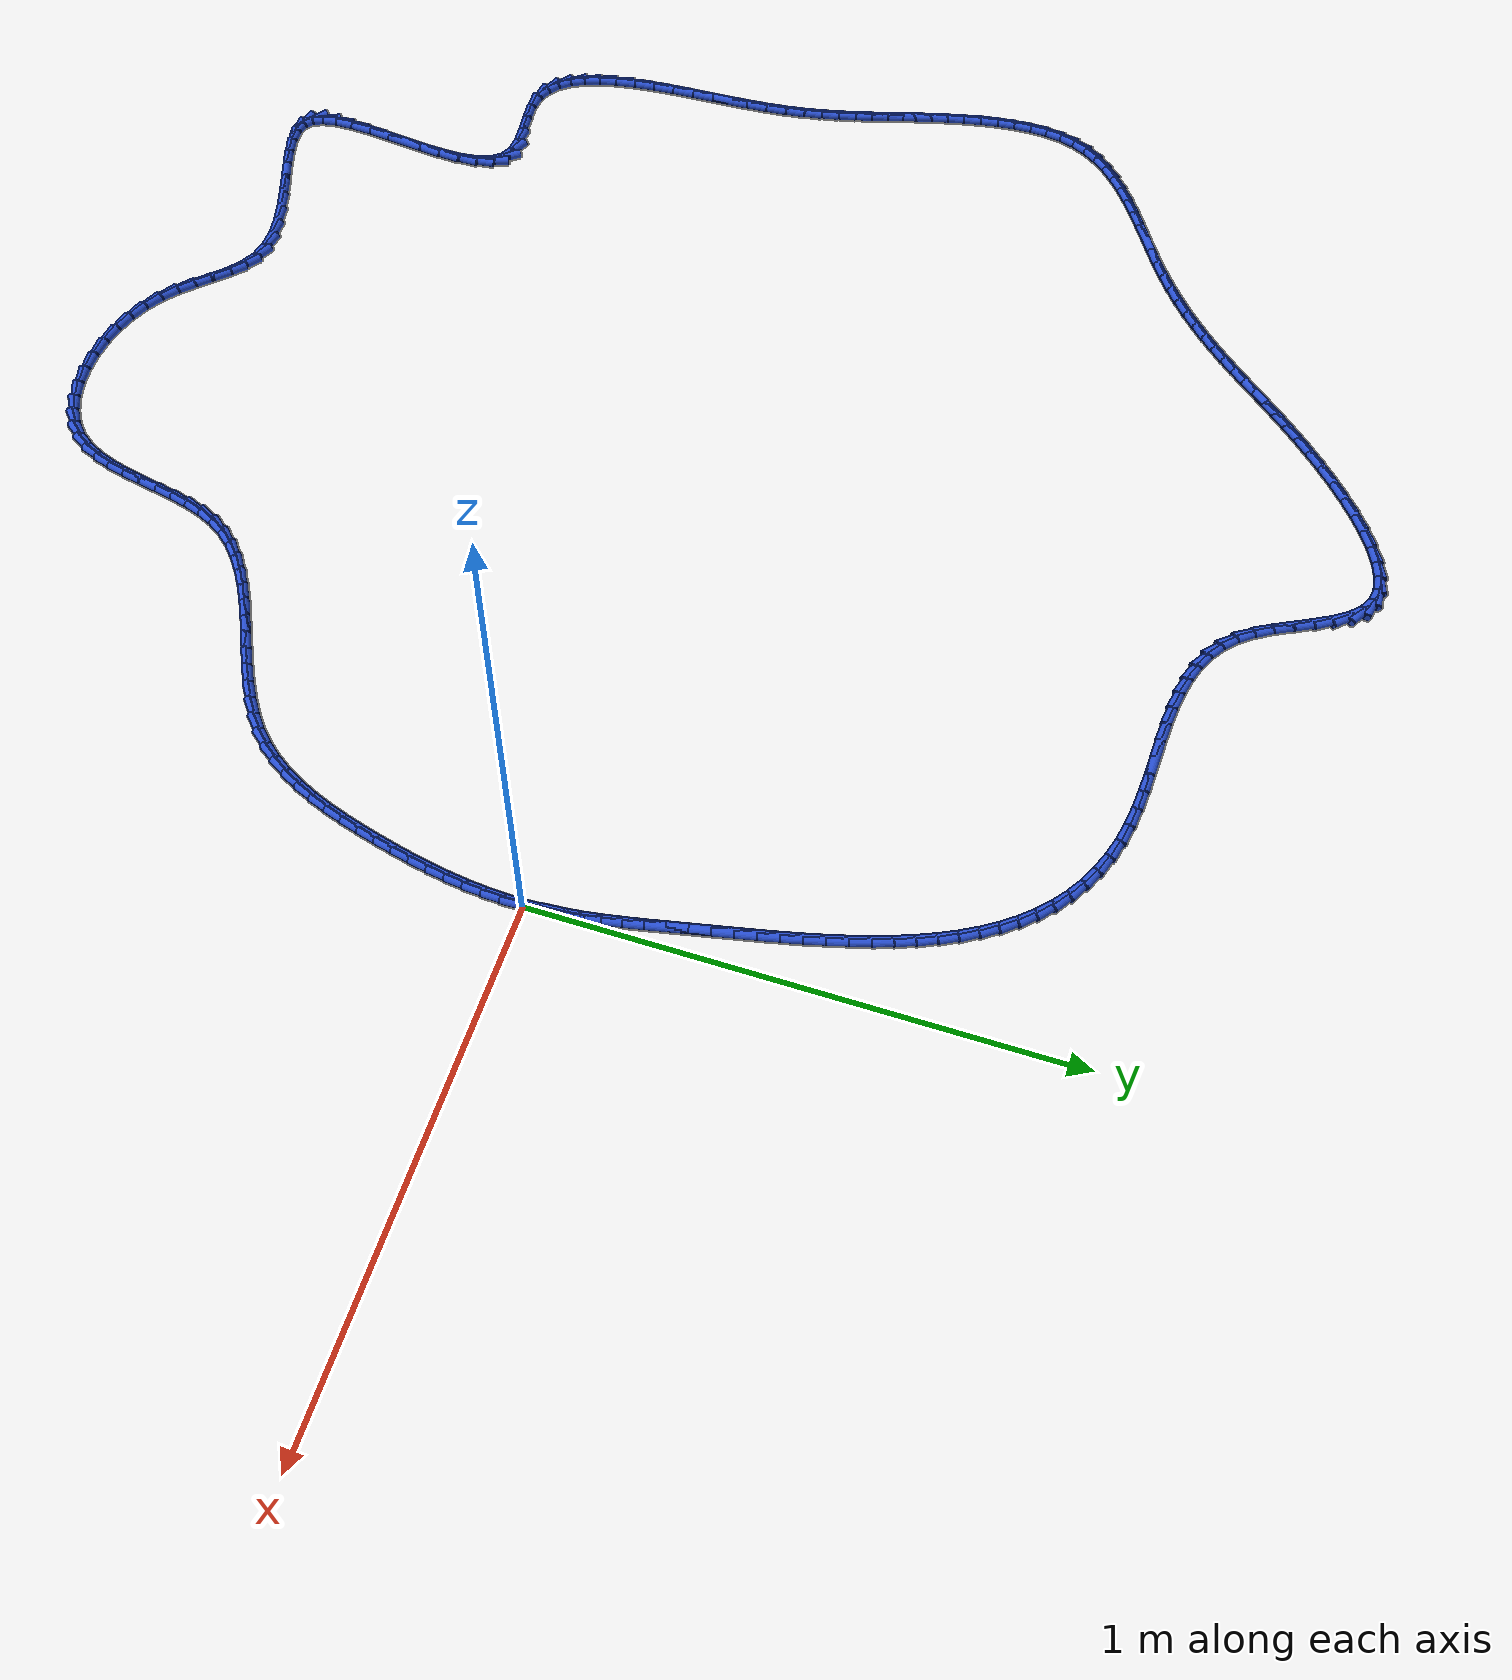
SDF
<sdf version="1.6">
 <world name="default">
  <light name="sun" type="directional">
   <pose>0 0 10 0 -0 0</pose>
   <diffuse>0.8 0.8 0.8 1</diffuse>
   <specular>0.2 0.2 0.2 1</specular>
   <attenuation>
    <range>1000</range>
    <constant>0.9</constant>
    <linear>0.01</linear>
    <quadratic>0.001</quadratic>
   </attenuation>
   <direction>-0.5 0.1 -0.9</direction>
  </light>
  <model name="ground_plane">
   <static>1</static>
   <link name="link">
    <collision name="collision">
     <geometry><plane><normal>0 0 1</normal><size>100 100</size></plane></geometry>
     <surface><friction><ode><mu>100</mu><mu2>50</mu2></ode></friction></surface>
    </collision>
    <visual name="visual">
     <cast_shadows>0</cast_shadows>
     <geometry><plane><normal>0 0 1</normal><size>100 100</size></plane></geometry>
     <material>
      <script><uri>file://media/materials/scripts/gazebo.material</uri><name>Gazebo/WhiteGlow</name></script>
     </material>
    </visual>
   </link>
  </model>
  <gravity>0 0 -9.8</gravity>
  <magnetic_field>6e-06 2.3e-05 -4.2e-05</magnetic_field>
  <atmosphere type="adiabatic"/>
  <physics name="default_physics" default="0" type="ode">
   <max_step_size>0.001</max_step_size>
   <real_time_factor>1</real_time_factor>
   <real_time_update_rate>1000</real_time_update_rate>
  </physics>
  <scene><ambient>0.4 0.4 0.4 1</ambient><background>0.7 0.7 0.7 1</background><shadows>1</shadows></scene>
  <spherical_coordinates>
   <surface_model>EARTH_WGS84</surface_model>
   <latitude_deg>0</latitude_deg>
   <longitude_deg>0</longitude_deg>
   <elevation>0</elevation>
   <heading_deg>0</heading_deg>
  </spherical_coordinates>
  <model name="line">
   <link name="link_0">
    <pose>-1.0408340855860843e-17 -1.249000902703301e-16 0.01 0 1.57 -1.5328114428045299</pose>
    <collision name="collision">
     <geometry><cylinder><radius>0.01</radius><length>0.08</length></cylinder></geometry>
    </collision>
    <visual name="visual">
     <material>
      <script><name>Gazebo/Blue</name><uri>file://media/materials/scripts/gazebo.material</uri></script>
     </material>
     <geometry><cylinder><radius>0.01</radius><length>0.08</length></cylinder></geometry>
    </visual>
   </link>
   <link name="link_1">
    <pose>-0.0013457381570896605 0.03541121414941874 0.01 0 1.57 -1.4879541787771837</pose>
    <collision name="collision">
     <geometry><cylinder><radius>0.01</radius><length>0.08</length></cylinder></geometry>
    </collision>
    <visual name="visual">
     <material>
      <script><name>Gazebo/Blue</name><uri>file://media/materials/scripts/gazebo.material</uri></script>
     </material>
     <geometry><cylinder><radius>0.01</radius><length>0.08</length></cylinder></geometry>
    </visual>
   </link>
   <link name="link_2">
    <pose>-0.004282115756074854 0.07077554638066325 0.01 0 1.57 -1.449849808840549</pose>
    <collision name="collision">
     <geometry><cylinder><radius>0.01</radius><length>0.08</length></cylinder></geometry>
    </collision>
    <visual name="visual">
     <material>
      <script><name>Gazebo/Blue</name><uri>file://media/materials/scripts/gazebo.material</uri></script>
     </material>
     <geometry><cylinder><radius>0.01</radius><length>0.08</length></cylinder></geometry>
    </visual>
   </link>
   <link name="link_3">
    <pose>-0.008585073144754691 0.106179257582286 0.01 0 1.57 -1.4187127974713785</pose>
    <collision name="collision">
     <geometry><cylinder><radius>0.01</radius><length>0.08</length></cylinder></geometry>
    </collision>
    <visual name="visual">
     <material>
      <script><name>Gazebo/Blue</name><uri>file://media/materials/scripts/gazebo.material</uri></script>
     </material>
     <geometry><cylinder><radius>0.01</radius><length>0.08</length></cylinder></geometry>
    </visual>
   </link>
   <link name="link_4">
    <pose>-0.014030550670928248 0.14170860864283966 0.01 0 1.57 -1.394587187264348</pose>
    <collision name="collision">
     <geometry><cylinder><radius>0.01</radius><length>0.08</length></cylinder></geometry>
    </collision>
    <visual name="visual">
     <material>
      <script><name>Gazebo/Blue</name><uri>file://media/materials/scripts/gazebo.material</uri></script>
     </material>
     <geometry><cylinder><radius>0.01</radius><length>0.08</length></cylinder></geometry>
    </visual>
   </link>
   <link name="link_5">
    <pose>-0.02039448868239461 0.17744986045087677 0.01 0 1.57 -1.3773937905006668</pose>
    <collision name="collision">
     <geometry><cylinder><radius>0.01</radius><length>0.08</length></cylinder></geometry>
    </collision>
    <visual name="visual">
     <material>
      <script><name>Gazebo/Blue</name><uri>file://media/materials/scripts/gazebo.material</uri></script>
     </material>
     <geometry><cylinder><radius>0.01</radius><length>0.08</length></cylinder></geometry>
    </visual>
   </link>
   <link name="link_6">
    <pose>-0.02745282752695288 0.2134892738949501 0.01 0 1.57 -1.3669701784389345</pose>
    <collision name="collision">
     <geometry><cylinder><radius>0.01</radius><length>0.08</length></cylinder></geometry>
    </collision>
    <visual name="visual">
     <material>
      <script><name>Gazebo/Blue</name><uri>file://media/materials/scripts/gazebo.material</uri></script>
     </material>
     <geometry><cylinder><radius>0.01</radius><length>0.08</length></cylinder></geometry>
    </visual>
   </link>
   <link name="link_7">
    <pose>-0.03498150755240213 0.2499131098636122 0.01 0 1.57 -1.3631004106243212</pose>
    <collision name="collision">
     <geometry><cylinder><radius>0.01</radius><length>0.08</length></cylinder></geometry>
    </collision>
    <visual name="visual">
     <material>
      <script><name>Gazebo/Blue</name><uri>file://media/materials/scripts/gazebo.material</uri></script>
     </material>
     <geometry><cylinder><radius>0.01</radius><length>0.08</length></cylinder></geometry>
    </visual>
   </link>
   <link name="link_8">
    <pose>-0.042756469106541455 0.28680762924541564 0.01 0 1.57 -1.3646808211759403</pose>
    <collision name="collision">
     <geometry><cylinder><radius>0.01</radius><length>0.08</length></cylinder></geometry>
    </collision>
    <visual name="visual">
     <material>
      <script><name>Gazebo/Blue</name><uri>file://media/materials/scripts/gazebo.material</uri></script>
     </material>
     <geometry><cylinder><radius>0.01</radius><length>0.08</length></cylinder></geometry>
    </visual>
   </link>
   <link name="link_9">
    <pose>-0.05058263239542309 0.3242381963017498 0.01 0 1.57 -1.3649883020470335</pose>
    <collision name="collision">
     <geometry><cylinder><radius>0.01</radius><length>0.08</length></cylinder></geometry>
    </collision>
    <visual name="visual">
     <material>
      <script><name>Gazebo/Blue</name><uri>file://media/materials/scripts/gazebo.material</uri></script>
     </material>
     <geometry><cylinder><radius>0.01</radius><length>0.08</length></cylinder></geometry>
    </visual>
   </link>
   <link name="link_10">
    <pose>-0.05848865682605078 0.3621088427359484 0.01 0 1.57 -1.3610593747516069</pose>
    <collision name="collision">
     <geometry><cylinder><radius>0.01</radius><length>0.08</length></cylinder></geometry>
    </collision>
    <visual name="visual">
     <material>
      <script><name>Gazebo/Blue</name><uri>file://media/materials/scripts/gazebo.material</uri></script>
     </material>
     <geometry><cylinder><radius>0.01</radius><length>0.08</length></cylinder></geometry>
    </visual>
   </link>
   <link name="link_11">
    <pose>-0.06660734931794815 0.4002485021704603 0.01 0 1.57 -1.3529351256896411</pose>
    <collision name="collision">
     <geometry><cylinder><radius>0.01</radius><length>0.08</length></cylinder></geometry>
    </collision>
    <visual name="visual">
     <material>
      <script><name>Gazebo/Blue</name><uri>file://media/materials/scripts/gazebo.material</uri></script>
     </material>
     <geometry><cylinder><radius>0.01</radius><length>0.08</length></cylinder></geometry>
    </visual>
   </link>
   <link name="link_12">
    <pose>-0.07507209685232474 0.4384856899602376 0.01 0 1.57 -1.3405846339166736</pose>
    <collision name="collision">
     <geometry><cylinder><radius>0.01</radius><length>0.08</length></cylinder></geometry>
    </collision>
    <visual name="visual">
     <material>
      <script><name>Gazebo/Blue</name><uri>file://media/materials/scripts/gazebo.material</uri></script>
     </material>
     <geometry><cylinder><radius>0.01</radius><length>0.08</length></cylinder></geometry>
    </visual>
   </link>
   <link name="link_13">
    <pose>-0.08401628641039006 0.4766489214602324 0.01 0 1.57 -1.3238931657171182</pose>
    <collision name="collision">
     <geometry><cylinder><radius>0.01</radius><length>0.08</length></cylinder></geometry>
    </collision>
    <visual name="visual">
     <material>
      <script><name>Gazebo/Blue</name><uri>file://media/materials/scripts/gazebo.material</uri></script>
     </material>
     <geometry><cylinder><radius>0.01</radius><length>0.08</length></cylinder></geometry>
    </visual>
   </link>
   <link name="link_14">
    <pose>-0.09357330497335362 0.5145667120253967 0.01 0 1.57 -1.302665730054357</pose>
    <collision name="collision">
     <geometry><cylinder><radius>0.01</radius><length>0.08</length></cylinder></geometry>
    </collision>
    <visual name="visual">
     <material>
      <script><name>Gazebo/Blue</name><uri>file://media/materials/scripts/gazebo.material</uri></script>
     </material>
     <geometry><cylinder><radius>0.01</radius><length>0.08</length></cylinder></geometry>
    </visual>
   </link>
   <link name="link_15">
    <pose>-0.10387653952242493 0.5520675770106828 0.01 0 1.57 -1.276630117853806</pose>
    <collision name="collision">
     <geometry><cylinder><radius>0.01</radius><length>0.08</length></cylinder></geometry>
    </collision>
    <visual name="visual">
     <material>
      <script><name>Gazebo/Blue</name><uri>file://media/materials/scripts/gazebo.material</uri></script>
     </material>
     <geometry><cylinder><radius>0.01</radius><length>0.08</length></cylinder></geometry>
    </visual>
   </link>
   <link name="link_16">
    <pose>-0.11505937703881346 0.5889800317710423 0.01 0 1.57 -1.245441064744905</pose>
    <collision name="collision">
     <geometry><cylinder><radius>0.01</radius><length>0.08</length></cylinder></geometry>
    </collision>
    <visual name="visual">
     <material>
      <script><name>Gazebo/Blue</name><uri>file://media/materials/scripts/gazebo.material</uri></script>
     </material>
     <geometry><cylinder><radius>0.01</radius><length>0.08</length></cylinder></geometry>
    </visual>
   </link>
   <link name="link_17">
    <pose>-0.12725520450372874 0.6251325916614273 0.01 0 1.57 -1.2086878591160524</pose>
    <collision name="collision">
     <geometry><cylinder><radius>0.01</radius><length>0.08</length></cylinder></geometry>
    </collision>
    <visual name="visual">
     <material>
      <script><name>Gazebo/Blue</name><uri>file://media/materials/scripts/gazebo.material</uri></script>
     </material>
     <geometry><cylinder><radius>0.01</radius><length>0.08</length></cylinder></geometry>
    </visual>
   </link>
   <link name="link_18">
    <pose>-0.1405974088983803 0.6603537720367901 0.01 0 1.57 -1.1659086810511956</pose>
    <collision name="collision">
     <geometry><cylinder><radius>0.01</radius><length>0.08</length></cylinder></geometry>
    </collision>
    <visual name="visual">
     <material>
      <script><name>Gazebo/Blue</name><uri>file://media/materials/scripts/gazebo.material</uri></script>
     </material>
     <geometry><cylinder><radius>0.01</radius><length>0.08</length></cylinder></geometry>
    </visual>
   </link>
   <link name="link_19">
    <pose>-0.15521937720397766 0.6944720882520826 0.01 0 1.57 -1.1166161307155849</pose>
    <collision name="collision">
     <geometry><cylinder><radius>0.01</radius><length>0.08</length></cylinder></geometry>
    </collision>
    <visual name="visual">
     <material>
      <script><name>Gazebo/Blue</name><uri>file://media/materials/scripts/gazebo.material</uri></script>
     </material>
     <geometry><cylinder><radius>0.01</radius><length>0.08</length></cylinder></geometry>
    </visual>
   </link>
   <link name="link_20">
    <pose>-0.17125449640173024 0.7273160556622567 0.01 0 1.57 -1.0603394749302981</pose>
    <collision name="collision">
     <geometry><cylinder><radius>0.01</radius><length>0.08</length></cylinder></geometry>
    </collision>
    <visual name="visual">
     <material>
      <script><name>Gazebo/Blue</name><uri>file://media/materials/scripts/gazebo.material</uri></script>
     </material>
     <geometry><cylinder><radius>0.01</radius><length>0.08</length></cylinder></geometry>
    </visual>
   </link>
   <link name="link_21">
    <pose>-0.18883615347284763 0.7587141896222646 0.01 0 1.57 -0.9966893404170106</pose>
    <collision name="collision">
     <geometry><cylinder><radius>0.01</radius><length>0.08</length></cylinder></geometry>
    </collision>
    <visual name="visual">
     <material>
      <script><name>Gazebo/Blue</name><uri>file://media/materials/scripts/gazebo.material</uri></script>
     </material>
     <geometry><cylinder><radius>0.01</radius><length>0.08</length></cylinder></geometry>
    </visual>
   </link>
   <link name="link_22">
    <pose>-0.2080977353985394 0.7884950054870585 0.01 0 1.57 -0.9254484787132689</pose>
    <collision name="collision">
     <geometry><cylinder><radius>0.01</radius><length>0.08</length></cylinder></geometry>
    </collision>
    <visual name="visual">
     <material>
      <script><name>Gazebo/Blue</name><uri>file://media/materials/scripts/gazebo.material</uri></script>
     </material>
     <geometry><cylinder><radius>0.01</radius><length>0.08</length></cylinder></geometry>
    </visual>
   </link>
   <link name="link_23">
    <pose>-0.22917262916001474 0.8164870186115893 0.01 0 1.57 -0.8466858286263065</pose>
    <collision name="collision">
     <geometry><cylinder><radius>0.01</radius><length>0.08</length></cylinder></geometry>
    </collision>
    <visual name="visual">
     <material>
      <script><name>Gazebo/Blue</name><uri>file://media/materials/scripts/gazebo.material</uri></script>
     </material>
     <geometry><cylinder><radius>0.01</radius><length>0.08</length></cylinder></geometry>
    </visual>
   </link>
   <link name="link_24">
    <pose>-0.25219422173848366 0.8425187443508112 0.01 0 1.57 -0.7608789018193167</pose>
    <collision name="collision">
     <geometry><cylinder><radius>0.01</radius><length>0.08</length></cylinder></geometry>
    </collision>
    <visual name="visual">
     <material>
      <script><name>Gazebo/Blue</name><uri>file://media/materials/scripts/gazebo.material</uri></script>
     </material>
     <geometry><cylinder><radius>0.01</radius><length>0.08</length></cylinder></geometry>
    </visual>
   </link>
   <link name="link_25">
    <pose>-0.2772959001151551 0.866418698059674 0.01 0 1.57 -0.669013049691923</pose>
    <collision name="collision">
     <geometry><cylinder><radius>0.01</radius><length>0.08</length></cylinder></geometry>
    </collision>
    <visual name="visual">
     <material>
      <script><name>Gazebo/Blue</name><uri>file://media/materials/scripts/gazebo.material</uri></script>
     </material>
     <geometry><cylinder><radius>0.01</radius><length>0.08</length></cylinder></geometry>
    </visual>
   </link>
   <link name="link_26">
    <pose>-0.30461105127123916 0.8880153950931314 0.01 0 1.57 -0.5729930037037516</pose>
    <collision name="collision">
     <geometry><cylinder><radius>0.01</radius><length>0.08</length></cylinder></geometry>
    </collision>
    <visual name="visual">
     <material>
      <script><name>Gazebo/Blue</name><uri>file://media/materials/scripts/gazebo.material</uri></script>
     </material>
     <geometry><cylinder><radius>0.01</radius><length>0.08</length></cylinder></geometry>
    </visual>
   </link>
   <link name="link_27">
    <pose>-0.3342555174768701 0.9071419848911536 0.01 0 1.57 -0.4790684563898968</pose>
    <collision name="collision">
     <geometry><cylinder><radius>0.01</radius><length>0.08</length></cylinder></geometry>
    </collision>
    <visual name="visual">
     <material>
      <script><name>Gazebo/Blue</name><uri>file://media/materials/scripts/gazebo.material</uri></script>
     </material>
     <geometry><cylinder><radius>0.01</radius><length>0.08</length></cylinder></geometry>
    </visual>
   </link>
   <link name="link_28">
    <pose>-0.36611720942789255 0.9236918204667054 0.01 0 1.57 -0.3902975250553778</pose>
    <collision name="collision">
     <geometry><cylinder><radius>0.01</radius><length>0.08</length></cylinder></geometry>
    </collision>
    <visual name="visual">
     <material>
      <script><name>Gazebo/Blue</name><uri>file://media/materials/scripts/gazebo.material</uri></script>
     </material>
     <geometry><cylinder><radius>0.01</radius><length>0.08</length></cylinder></geometry>
    </visual>
   </link>
   <link name="link_29">
    <pose>-0.39992473778868326 0.9376003307544477 0.01 0 1.57 -0.3058704722440527</pose>
    <collision name="collision">
     <geometry><cylinder><radius>0.01</radius><length>0.08</length></cylinder></geometry>
    </collision>
    <visual name="visual">
     <material>
      <script><name>Gazebo/Blue</name><uri>file://media/materials/scripts/gazebo.material</uri></script>
     </material>
     <geometry><cylinder><radius>0.01</radius><length>0.08</length></cylinder></geometry>
    </visual>
   </link>
   <link name="link_30">
    <pose>-0.4354034494841761 0.9488038067406316 0.01 0 1.57 -0.22563336026927192</pose>
    <collision name="collision">
     <geometry><cylinder><radius>0.01</radius><length>0.08</length></cylinder></geometry>
    </collision>
    <visual name="visual">
     <material>
      <script><name>Gazebo/Blue</name><uri>file://media/materials/scripts/gazebo.material</uri></script>
     </material>
     <geometry><cylinder><radius>0.01</radius><length>0.08</length></cylinder></geometry>
    </visual>
   </link>
   <link name="link_31">
    <pose>-0.4722766214476121 0.9572677485677066 0.01 0 1.57 -0.15825387505653035</pose>
    <collision name="collision">
     <geometry><cylinder><radius>0.01</radius><length>0.08</length></cylinder></geometry>
    </collision>
    <visual name="visual">
     <material>
      <script><name>Gazebo/Blue</name><uri>file://media/materials/scripts/gazebo.material</uri></script>
     </material>
     <geometry><cylinder><radius>0.01</radius><length>0.08</length></cylinder></geometry>
    </visual>
   </link>
   <link name="link_32">
    <pose>-0.5102413925524618 0.9633264842693678 0.01 0 1.57 -0.10903848361394776</pose>
    <collision name="collision">
     <geometry><cylinder><radius>0.01</radius><length>0.08</length></cylinder></geometry>
    </collision>
    <visual name="visual">
     <material>
      <script><name>Gazebo/Blue</name><uri>file://media/materials/scripts/gazebo.material</uri></script>
     </material>
     <geometry><cylinder><radius>0.01</radius><length>0.08</length></cylinder></geometry>
    </visual>
   </link>
   <link name="link_33">
    <pose>-0.5489769980985191 0.9675669749126167 0.01 0 1.57 -0.07676866494923182</pose>
    <collision name="collision">
     <geometry><cylinder><radius>0.01</radius><length>0.08</length></cylinder></geometry>
    </collision>
    <visual name="visual">
     <material>
      <script><name>Gazebo/Blue</name><uri>file://media/materials/scripts/gazebo.material</uri></script>
     </material>
     <geometry><cylinder><radius>0.01</radius><length>0.08</length></cylinder></geometry>
    </visual>
   </link>
   <link name="link_34">
    <pose>-0.588162324569635 0.9705811036225443 0.01 0 1.57 -0.06045566654952272</pose>
    <collision name="collision">
     <geometry><cylinder><radius>0.01</radius><length>0.08</length></cylinder></geometry>
    </collision>
    <visual name="visual">
     <material>
      <script><name>Gazebo/Blue</name><uri>file://media/materials/scripts/gazebo.material</uri></script>
     </material>
     <geometry><cylinder><radius>0.01</radius><length>0.08</length></cylinder></geometry>
    </visual>
   </link>
   <link name="link_35">
    <pose>-0.6274762584496614 0.9729607535242414 0.01 0 1.57 -0.05966755865339196</pose>
    <collision name="collision">
     <geometry><cylinder><radius>0.01</radius><length>0.08</length></cylinder></geometry>
    </collision>
    <visual name="visual">
     <material>
      <script><name>Gazebo/Blue</name><uri>file://media/materials/scripts/gazebo.material</uri></script>
     </material>
     <geometry><cylinder><radius>0.01</radius><length>0.08</length></cylinder></geometry>
    </visual>
   </link>
   <link name="link_36">
    <pose>-0.666597686222449 0.9752978077427991 0.01 0 1.57 -0.07462175058128107</pose>
    <collision name="collision">
     <geometry><cylinder><radius>0.01</radius><length>0.08</length></cylinder></geometry>
    </collision>
    <visual name="visual">
     <material>
      <script><name>Gazebo/Blue</name><uri>file://media/materials/scripts/gazebo.material</uri></script>
     </material>
     <geometry><cylinder><radius>0.01</radius><length>0.08</length></cylinder></geometry>
    </visual>
   </link>
   <link name="link_37">
    <pose>-0.7052054943718502 0.9781841494033086 0.01 0 1.57 -0.10622256811869774</pose>
    <collision name="collision">
     <geometry><cylinder><radius>0.01</radius><length>0.08</length></cylinder></geometry>
    </collision>
    <visual name="visual">
     <material>
      <script><name>Gazebo/Blue</name><uri>file://media/materials/scripts/gazebo.material</uri></script>
     </material>
     <geometry><cylinder><radius>0.01</radius><length>0.08</length></cylinder></geometry>
    </visual>
   </link>
   <link name="link_38">
    <pose>-0.7429785693817154 0.9822116616308608 0.01 0 1.57 -0.1560395663719989</pose>
    <collision name="collision">
     <geometry><cylinder><radius>0.01</radius><length>0.08</length></cylinder></geometry>
    </collision>
    <visual name="visual">
     <material>
      <script><name>Gazebo/Blue</name><uri>file://media/materials/scripts/gazebo.material</uri></script>
     </material>
     <geometry><cylinder><radius>0.01</radius><length>0.08</length></cylinder></geometry>
    </visual>
   </link>
   <link name="link_39">
    <pose>-0.779595797735896 0.9879722275505466 0.01 0 1.57 -0.22615598423063824</pose>
    <collision name="collision">
     <geometry><cylinder><radius>0.01</radius><length>0.08</length></cylinder></geometry>
    </collision>
    <visual name="visual">
     <material>
      <script><name>Gazebo/Blue</name><uri>file://media/materials/scripts/gazebo.material</uri></script>
     </material>
     <geometry><cylinder><radius>0.01</radius><length>0.08</length></cylinder></geometry>
    </visual>
   </link>
   <link name="link_40">
    <pose>-0.8147360659182442 0.996057730287457 0.01 0 1.57 -0.31873129166913367</pose>
    <collision name="collision">
     <geometry><cylinder><radius>0.01</radius><length>0.08</length></cylinder></geometry>
    </collision>
    <visual name="visual">
     <material>
      <script><name>Gazebo/Blue</name><uri>file://media/materials/scripts/gazebo.material</uri></script>
     </material>
     <geometry><cylinder><radius>0.01</radius><length>0.08</length></cylinder></geometry>
    </visual>
   </link>
   <link name="link_41">
    <pose>-0.8480782604126106 1.007060052966683 0.01 0 1.57 -0.43505560503989893</pose>
    <collision name="collision">
     <geometry><cylinder><radius>0.01</radius><length>0.08</length></cylinder></geometry>
    </collision>
    <visual name="visual">
     <material>
      <script><name>Gazebo/Blue</name><uri>file://media/materials/scripts/gazebo.material</uri></script>
     </material>
     <geometry><cylinder><radius>0.01</radius><length>0.08</length></cylinder></geometry>
    </visual>
   </link>
   <link name="link_42">
    <pose>-0.8793012677028467 1.0215710787133159 0.01 0 1.57 -0.5739988374188456</pose>
    <collision name="collision">
     <geometry><cylinder><radius>0.01</radius><length>0.08</length></cylinder></geometry>
    </collision>
    <visual name="visual">
     <material>
      <script><name>Gazebo/Blue</name><uri>file://media/materials/scripts/gazebo.material</uri></script>
     </material>
     <geometry><cylinder><radius>0.01</radius><length>0.08</length></cylinder></geometry>
    </visual>
   </link>
   <link name="link_43">
    <pose>-0.9080839742728042 1.0401826906524465 0.01 0 1.57 -0.7303662945092938</pose>
    <collision name="collision">
     <geometry><cylinder><radius>0.01</radius><length>0.08</length></cylinder></geometry>
    </collision>
    <visual name="visual">
     <material>
      <script><name>Gazebo/Blue</name><uri>file://media/materials/scripts/gazebo.material</uri></script>
     </material>
     <geometry><cylinder><radius>0.01</radius><length>0.08</length></cylinder></geometry>
    </visual>
   </link>
   <link name="link_44">
    <pose>-0.9341052666063341 1.0634867719091659 0.01 0 1.57 -0.8926601107316539</pose>
    <collision name="collision">
     <geometry><cylinder><radius>0.01</radius><length>0.08</length></cylinder></geometry>
    </collision>
    <visual name="visual">
     <material>
      <script><name>Gazebo/Blue</name><uri>file://media/materials/scripts/gazebo.material</uri></script>
     </material>
     <geometry><cylinder><radius>0.01</radius><length>0.08</length></cylinder></geometry>
    </visual>
   </link>
   <link name="link_45">
    <pose>-0.9570783934508018 1.092004149261729 0.01 0 1.57 -1.0175275707164992</pose>
    <collision name="collision">
     <geometry><cylinder><radius>0.01</radius><length>0.08</length></cylinder></geometry>
    </collision>
    <visual name="visual">
     <material>
      <script><name>Gazebo/Blue</name><uri>file://media/materials/scripts/gazebo.material</uri></script>
     </material>
     <geometry><cylinder><radius>0.01</radius><length>0.08</length></cylinder></geometry>
    </visual>
   </link>
   <link name="link_46">
    <pose>-0.9773823167017044 1.1248790479636468 0.01 0 1.57 -1.083480997667562</pose>
    <collision name="collision">
     <geometry><cylinder><radius>0.01</radius><length>0.08</length></cylinder></geometry>
    </collision>
    <visual name="visual">
     <material>
      <script><name>Gazebo/Blue</name><uri>file://media/materials/scripts/gazebo.material</uri></script>
     </material>
     <geometry><cylinder><radius>0.01</radius><length>0.08</length></cylinder></geometry>
    </visual>
   </link>
   <link name="link_47">
    <pose>-0.9959990588463544 1.1600086484526022 0.01 0 1.57 -1.1000188340280084</pose>
    <collision name="collision">
     <geometry><cylinder><radius>0.01</radius><length>0.08</length></cylinder></geometry>
    </collision>
    <visual name="visual">
     <material>
      <script><name>Gazebo/Blue</name><uri>file://media/materials/scripts/gazebo.material</uri></script>
     </material>
     <geometry><cylinder><radius>0.01</radius><length>0.08</length></cylinder></geometry>
    </visual>
   </link>
   <link name="link_48">
    <pose>-1.013932435736309 1.1952450655422457 0.01 0 1.57 -1.0680367100440324</pose>
    <collision name="collision">
     <geometry><cylinder><radius>0.01</radius><length>0.08</length></cylinder></geometry>
    </collision>
    <visual name="visual">
     <material>
      <script><name>Gazebo/Blue</name><uri>file://media/materials/scripts/gazebo.material</uri></script>
     </material>
     <geometry><cylinder><radius>0.01</radius><length>0.08</length></cylinder></geometry>
    </visual>
   </link>
   <link name="link_49">
    <pose>-1.032186263223125 1.228440414046227 0.01 0 1.57 -0.9770756146621083</pose>
    <collision name="collision">
     <geometry><cylinder><radius>0.01</radius><length>0.08</length></cylinder></geometry>
    </collision>
    <visual name="visual">
     <material>
      <script><name>Gazebo/Blue</name><uri>file://media/materials/scripts/gazebo.material</uri></script>
     </material>
     <geometry><cylinder><radius>0.01</radius><length>0.08</length></cylinder></geometry>
    </visual>
   </link>
   <link name="link_50">
    <pose>-1.0517643571583584 1.2574468087781963 0.01 0 1.57 -0.8025219410421227</pose>
    <collision name="collision">
     <geometry><cylinder><radius>0.01</radius><length>0.08</length></cylinder></geometry>
    </collision>
    <visual name="visual">
     <material>
      <script><name>Gazebo/Blue</name><uri>file://media/materials/scripts/gazebo.material</uri></script>
     </material>
     <geometry><cylinder><radius>0.01</radius><length>0.08</length></cylinder></geometry>
    </visual>
   </link>
   <link name="link_51">
    <pose>-1.0736705333935666 1.2801163645518037 0.01 0 1.57 -0.5157008101195532</pose>
    <collision name="collision">
     <geometry><cylinder><radius>0.01</radius><length>0.08</length></cylinder></geometry>
    </collision>
    <visual name="visual">
     <material>
      <script><name>Gazebo/Blue</name><uri>file://media/materials/scripts/gazebo.material</uri></script>
     </material>
     <geometry><cylinder><radius>0.01</radius><length>0.08</length></cylinder></geometry>
    </visual>
   </link>
   <link name="link_52">
    <pose>-1.0988598838376158 1.2943953819164875 0.01 0 1.57 -0.18938155266959492</pose>
    <collision name="collision">
     <geometry><cylinder><radius>0.01</radius><length>0.08</length></cylinder></geometry>
    </collision>
    <visual name="visual">
     <material>
      <script><name>Gazebo/Blue</name><uri>file://media/materials/scripts/gazebo.material</uri></script>
     </material>
     <geometry><cylinder><radius>0.01</radius><length>0.08</length></cylinder></geometry>
    </visual>
   </link>
   <link name="link_53">
    <pose>-1.1274375725391494 1.29987311304801 0.01 0 1.57 0.07445049427166867</pose>
    <collision name="collision">
     <geometry><cylinder><radius>0.01</radius><length>0.08</length></cylinder></geometry>
    </collision>
    <visual name="visual">
     <material>
      <script><name>Gazebo/Blue</name><uri>file://media/materials/scripts/gazebo.material</uri></script>
     </material>
     <geometry><cylinder><radius>0.01</radius><length>0.08</length></cylinder></geometry>
    </visual>
   </link>
   <link name="link_54">
    <pose>-1.1587865712377918 1.297534842755186 0.01 0 1.57 0.26607413426901294</pose>
    <collision name="collision">
     <geometry><cylinder><radius>0.01</radius><length>0.08</length></cylinder></geometry>
    </collision>
    <visual name="visual">
     <material>
      <script><name>Gazebo/Blue</name><uri>file://media/materials/scripts/gazebo.material</uri></script>
     </material>
     <geometry><cylinder><radius>0.01</radius><length>0.08</length></cylinder></geometry>
    </visual>
   </link>
   <link name="link_55">
    <pose>-1.1922668874397386 1.288410246819792 0.01 0 1.57 0.4023137461545978</pose>
    <collision name="collision">
     <geometry><cylinder><radius>0.01</radius><length>0.08</length></cylinder></geometry>
    </collision>
    <visual name="visual">
     <material>
      <script><name>Gazebo/Blue</name><uri>file://media/materials/scripts/gazebo.material</uri></script>
     </material>
     <geometry><cylinder><radius>0.01</radius><length>0.08</length></cylinder></geometry>
    </visual>
   </link>
   <link name="link_56">
    <pose>-1.2272385286511858 1.2735290010236044 0.01 0 1.57 0.5008174520608945</pose>
    <collision name="collision">
     <geometry><cylinder><radius>0.01</radius><length>0.08</length></cylinder></geometry>
    </collision>
    <visual name="visual">
     <material>
      <script><name>Gazebo/Blue</name><uri>file://media/materials/scripts/gazebo.material</uri></script>
     </material>
     <geometry><cylinder><radius>0.01</radius><length>0.08</length></cylinder></geometry>
    </visual>
   </link>
   <link name="link_57">
    <pose>-1.2630615023783271 1.2539207811483994 0.01 0 1.57 0.5740934905510577</pose>
    <collision name="collision">
     <geometry><cylinder><radius>0.01</radius><length>0.08</length></cylinder></geometry>
    </collision>
    <visual name="visual">
     <material>
      <script><name>Gazebo/Blue</name><uri>file://media/materials/scripts/gazebo.material</uri></script>
     </material>
     <geometry><cylinder><radius>0.01</radius><length>0.08</length></cylinder></geometry>
    </visual>
   </link>
   <link name="link_58">
    <pose>-1.2990958161273587 1.2306152629759537 0.01 0 1.57 0.6302297011941482</pose>
    <collision name="collision">
     <geometry><cylinder><radius>0.01</radius><length>0.08</length></cylinder></geometry>
    </collision>
    <visual name="visual">
     <material>
      <script><name>Gazebo/Blue</name><uri>file://media/materials/scripts/gazebo.material</uri></script>
     </material>
     <geometry><cylinder><radius>0.01</radius><length>0.08</length></cylinder></geometry>
    </visual>
   </link>
   <link name="link_59">
    <pose>-1.3347014774044754 1.2046421222880435 0.01 0 1.57 0.6744137839557371</pose>
    <collision name="collision">
     <geometry><cylinder><radius>0.01</radius><length>0.08</length></cylinder></geometry>
    </collision>
    <visual name="visual">
     <material>
      <script><name>Gazebo/Blue</name><uri>file://media/materials/scripts/gazebo.material</uri></script>
     </material>
     <geometry><cylinder><radius>0.01</radius><length>0.08</length></cylinder></geometry>
    </visual>
   </link>
   <link name="link_60">
    <pose>-1.3692384937158733 1.1770310348664448 0.01 0 1.57 0.7100424940325585</pose>
    <collision name="collision">
     <geometry><cylinder><radius>0.01</radius><length>0.08</length></cylinder></geometry>
    </collision>
    <visual name="visual">
     <material>
      <script><name>Gazebo/Blue</name><uri>file://media/materials/scripts/gazebo.material</uri></script>
     </material>
     <geometry><cylinder><radius>0.01</radius><length>0.08</length></cylinder></geometry>
    </visual>
   </link>
   <link name="link_61">
    <pose>-1.4020668725677454 1.1488116764929341 0.01 0 1.57 0.7397726572771555</pose>
    <collision name="collision">
     <geometry><cylinder><radius>0.01</radius><length>0.08</length></cylinder></geometry>
    </collision>
    <visual name="visual">
     <material>
      <script><name>Gazebo/Blue</name><uri>file://media/materials/scripts/gazebo.material</uri></script>
     </material>
     <geometry><cylinder><radius>0.01</radius><length>0.08</length></cylinder></geometry>
    </visual>
   </link>
   <link name="link_62">
    <pose>-1.4326790900577868 1.1208727402609795 0.01 0 1.57 0.7661713701273847</pose>
    <collision name="collision">
     <geometry><cylinder><radius>0.01</radius><length>0.08</length></cylinder></geometry>
    </collision>
    <visual name="visual">
     <material>
      <script><name>Gazebo/Blue</name><uri>file://media/materials/scripts/gazebo.material</uri></script>
     </material>
     <geometry><cylinder><radius>0.01</radius><length>0.08</length></cylinder></geometry>
    </visual>
   </link>
   <link name="link_63">
    <pose>-1.4612185690662745 1.0934101344588634 0.01 0 1.57 0.7889852936206178</pose>
    <collision name="collision">
     <geometry><cylinder><radius>0.01</radius><length>0.08</length></cylinder></geometry>
    </collision>
    <visual name="visual">
     <material>
      <script><name>Gazebo/Blue</name><uri>file://media/materials/scripts/gazebo.material</uri></script>
     </material>
     <geometry><cylinder><radius>0.01</radius><length>0.08</length></cylinder></geometry>
    </visual>
   </link>
   <link name="link_64">
    <pose>-1.4880283501293594 1.0664073197792483 0.01 0 1.57 0.8072565799552895</pose>
    <collision name="collision">
     <geometry><cylinder><radius>0.01</radius><length>0.08</length></cylinder></geometry>
    </collision>
    <visual name="visual">
     <material>
      <script><name>Gazebo/Blue</name><uri>file://media/materials/scripts/gazebo.material</uri></script>
     </material>
     <geometry><cylinder><radius>0.01</radius><length>0.08</length></cylinder></geometry>
    </visual>
   </link>
   <link name="link_65">
    <pose>-1.5134515262422163 1.039847701084096 0.01 0 1.57 0.8200953908142818</pose>
    <collision name="collision">
     <geometry><cylinder><radius>0.01</radius><length>0.08</length></cylinder></geometry>
    </collision>
    <visual name="visual">
     <material>
      <script><name>Gazebo/Blue</name><uri>file://media/materials/scripts/gazebo.material</uri></script>
     </material>
     <geometry><cylinder><radius>0.01</radius><length>0.08</length></cylinder></geometry>
    </visual>
   </link>
   <link name="link_66">
    <pose>-1.5378311904000213 1.0137146832353696 0.01 0 1.57 0.8267444965421188</pose>
    <collision name="collision">
     <geometry><cylinder><radius>0.01</radius><length>0.08</length></cylinder></geometry>
    </collision>
    <visual name="visual">
     <material>
      <script><name>Gazebo/Blue</name><uri>file://media/materials/scripts/gazebo.material</uri></script>
     </material>
     <geometry><cylinder><radius>0.01</radius><length>0.08</length></cylinder></geometry>
    </visual>
   </link>
   <link name="link_67">
    <pose>-1.5615104355979477 0.9879916710950323 0.01 0 1.57 0.8266413520631027</pose>
    <collision name="collision">
     <geometry><cylinder><radius>0.01</radius><length>0.08</length></cylinder></geometry>
    </collision>
    <visual name="visual">
     <material>
      <script><name>Gazebo/Blue</name><uri>file://media/materials/scripts/gazebo.material</uri></script>
     </material>
     <geometry><cylinder><radius>0.01</radius><length>0.08</length></cylinder></geometry>
    </visual>
   </link>
   <link name="link_68">
    <pose>-1.5848323548311714 0.9626620695250462 0.01 0 1.57 0.8194729049188039</pose>
    <collision name="collision">
     <geometry><cylinder><radius>0.01</radius><length>0.08</length></cylinder></geometry>
    </collision>
    <visual name="visual">
     <material>
      <script><name>Gazebo/Blue</name><uri>file://media/materials/scripts/gazebo.material</uri></script>
     </material>
     <geometry><cylinder><radius>0.01</radius><length>0.08</length></cylinder></geometry>
    </visual>
   </link>
   <link name="link_69">
    <pose>-1.6081400410948663 0.9377092833873734 0.01 0 1.57 0.8052180258226997</pose>
    <collision name="collision">
     <geometry><cylinder><radius>0.01</radius><length>0.08</length></cylinder></geometry>
    </collision>
    <visual name="visual">
     <material>
      <script><name>Gazebo/Blue</name><uri>file://media/materials/scripts/gazebo.material</uri></script>
     </material>
     <geometry><cylinder><radius>0.01</radius><length>0.08</length></cylinder></geometry>
    </visual>
   </link>
   <link name="link_70">
    <pose>-1.631776587384207 0.9131167175439773 0.01 0 1.57 0.784171603818898</pose>
    <collision name="collision">
     <geometry><cylinder><radius>0.01</radius><length>0.08</length></cylinder></geometry>
    </collision>
    <visual name="visual">
     <material>
      <script><name>Gazebo/Blue</name><uri>file://media/materials/scripts/gazebo.material</uri></script>
     </material>
     <geometry><cylinder><radius>0.01</radius><length>0.08</length></cylinder></geometry>
    </visual>
   </link>
   <link name="link_71">
    <pose>-1.6560850866943693 0.8888677768568212 0.01 0 1.57 0.7574339520146466</pose>
    <collision name="collision">
     <geometry><cylinder><radius>0.01</radius><length>0.08</length></cylinder></geometry>
    </collision>
    <visual name="visual">
     <material>
      <script><name>Gazebo/Blue</name><uri>file://media/materials/scripts/gazebo.material</uri></script>
     </material>
     <geometry><cylinder><radius>0.01</radius><length>0.08</length></cylinder></geometry>
    </visual>
   </link>
   <link name="link_72">
    <pose>-1.681370363333642 0.8649585445702962 0.01 0 1.57 0.7279893042419832</pose>
    <collision name="collision">
     <geometry><cylinder><radius>0.01</radius><length>0.08</length></cylinder></geometry>
    </collision>
    <visual name="visual">
     <material>
      <script><name>Gazebo/Blue</name><uri>file://media/materials/scripts/gazebo.material</uri></script>
     </material>
     <geometry><cylinder><radius>0.01</radius><length>0.08</length></cylinder></geometry>
    </visual>
   </link>
   <link name="link_73">
    <pose>-1.707748496524687 0.8414476350102633 0.01 0 1.57 0.6967481591814403</pose>
    <collision name="collision">
     <geometry><cylinder><radius>0.01</radius><length>0.08</length></cylinder></geometry>
    </collision>
    <visual name="visual">
     <material>
      <script><name>Gazebo/Blue</name><uri>file://media/materials/scripts/gazebo.material</uri></script>
     </material>
     <geometry><cylinder><radius>0.01</radius><length>0.08</length></cylinder></geometry>
    </visual>
   </link>
   <link name="link_74">
    <pose>-1.735277476405817 0.818412907365323 0.01 0 1.57 0.6638352588885517</pose>
    <collision name="collision">
     <geometry><cylinder><radius>0.01</radius><length>0.08</length></cylinder></geometry>
    </collision>
    <visual name="visual">
     <material>
      <script><name>Gazebo/Blue</name><uri>file://media/materials/scripts/gazebo.material</uri></script>
     </material>
     <geometry><cylinder><radius>0.01</radius><length>0.08</length></cylinder></geometry>
    </visual>
   </link>
   <link name="link_75">
    <pose>-1.7640152770739914 0.7959322261385633 0.01 0 1.57 0.6293899566559076</pose>
    <collision name="collision">
     <geometry><cylinder><radius>0.01</radius><length>0.08</length></cylinder></geometry>
    </collision>
    <visual name="visual">
     <material>
      <script><name>Gazebo/Blue</name><uri>file://media/materials/scripts/gazebo.material</uri></script>
     </material>
     <geometry><cylinder><radius>0.01</radius><length>0.08</length></cylinder></geometry>
    </visual>
   </link>
   <link name="link_76">
    <pose>-1.7940198726261685 0.7740834558330704 0.01 0 1.57 0.5935670678103601</pose>
    <collision name="collision">
     <geometry><cylinder><radius>0.01</radius><length>0.08</length></cylinder></geometry>
    </collision>
    <visual name="visual">
     <material>
      <script><name>Gazebo/Blue</name><uri>file://media/materials/scripts/gazebo.material</uri></script>
     </material>
     <geometry><cylinder><radius>0.01</radius><length>0.08</length></cylinder></geometry>
    </visual>
   </link>
   <link name="link_77">
    <pose>-1.8253492371593074 0.7529444609519327 0.01 0 1.57 0.5574463275758754</pose>
    <collision name="collision">
     <geometry><cylinder><radius>0.01</radius><length>0.08</length></cylinder></geometry>
    </collision>
    <visual name="visual">
     <material>
      <script><name>Gazebo/Blue</name><uri>file://media/materials/scripts/gazebo.material</uri></script>
     </material>
     <geometry><cylinder><radius>0.01</radius><length>0.08</length></cylinder></geometry>
    </visual>
   </link>
   <link name="link_78">
    <pose>-1.8580286419655099 0.7325721925354326 0.01 0 1.57 0.5302896894429907</pose>
    <collision name="collision">
     <geometry><cylinder><radius>0.01</radius><length>0.08</length></cylinder></geometry>
    </collision>
    <visual name="visual">
     <material>
      <script><name>Gazebo/Blue</name><uri>file://media/materials/scripts/gazebo.material</uri></script>
     </material>
     <geometry><cylinder><radius>0.01</radius><length>0.08</length></cylinder></geometry>
    </visual>
   </link>
   <link name="link_79">
    <pose>-1.8917424391536246 0.7128055836070596 0.01 0 1.57 0.5167568934821275</pose>
    <collision name="collision">
     <geometry><cylinder><radius>0.01</radius><length>0.08</length></cylinder></geometry>
    </collision>
    <visual name="visual">
     <material>
      <script><name>Gazebo/Blue</name><uri>file://media/materials/scripts/gazebo.material</uri></script>
     </material>
     <geometry><cylinder><radius>0.01</radius><length>0.08</length></cylinder></geometry>
    </visual>
   </link>
   <link name="link_80">
    <pose>-1.9259723413863357 0.6933539791461382 0.01 0 1.57 0.5163178331271729</pose>
    <collision name="collision">
     <geometry><cylinder><radius>0.01</radius><length>0.08</length></cylinder></geometry>
    </collision>
    <visual name="visual">
     <material>
      <script><name>Gazebo/Blue</name><uri>file://media/materials/scripts/gazebo.material</uri></script>
     </material>
     <geometry><cylinder><radius>0.01</radius><length>0.08</length></cylinder></geometry>
    </visual>
   </link>
   <link name="link_81">
    <pose>-1.9601973829031427 0.6739250112788004 0.01 0 1.57 0.5289778249538523</pose>
    <collision name="collision">
     <geometry><cylinder><radius>0.01</radius><length>0.08</length></cylinder></geometry>
    </collision>
    <visual name="visual">
     <material>
      <script><name>Gazebo/Blue</name><uri>file://media/materials/scripts/gazebo.material</uri></script>
     </material>
     <geometry><cylinder><radius>0.01</radius><length>0.08</length></cylinder></geometry>
    </visual>
   </link>
   <link name="link_82">
    <pose>-1.9938965979435455 0.6542263121311791 0.01 0 1.57 0.5553561493418969</pose>
    <collision name="collision">
     <geometry><cylinder><radius>0.01</radius><length>0.08</length></cylinder></geometry>
    </collision>
    <visual name="visual">
     <material>
      <script><name>Gazebo/Blue</name><uri>file://media/materials/scripts/gazebo.material</uri></script>
     </material>
     <geometry><cylinder><radius>0.01</radius><length>0.08</length></cylinder></geometry>
    </visual>
   </link>
   <link name="link_83">
    <pose>-2.026549020747043 0.6339655138294075 0.01 0 1.57 0.5966857856951837</pose>
    <collision name="collision">
     <geometry><cylinder><radius>0.01</radius><length>0.08</length></cylinder></geometry>
    </collision>
    <visual name="visual">
     <material>
      <script><name>Gazebo/Blue</name><uri>file://media/materials/scripts/gazebo.material</uri></script>
     </material>
     <geometry><cylinder><radius>0.01</radius><length>0.08</length></cylinder></geometry>
    </visual>
   </link>
   <link name="link_84">
    <pose>-2.057633685553135 0.612850248499618 0.01 0 1.57 0.6547747847410307</pose>
    <collision name="collision">
     <geometry><cylinder><radius>0.01</radius><length>0.08</length></cylinder></geometry>
    </collision>
    <visual name="visual">
     <material>
      <script><name>Gazebo/Blue</name><uri>file://media/materials/scripts/gazebo.material</uri></script>
     </material>
     <geometry><cylinder><radius>0.01</radius><length>0.08</length></cylinder></geometry>
    </visual>
   </link>
   <link name="link_85">
    <pose>-2.0866296266013222 0.5905881482679429 0.01 0 1.57 0.7318443168884475</pose>
    <collision name="collision">
     <geometry><cylinder><radius>0.01</radius><length>0.08</length></cylinder></geometry>
    </collision>
    <visual name="visual">
     <material>
      <script><name>Gazebo/Blue</name><uri>file://media/materials/scripts/gazebo.material</uri></script>
     </material>
     <geometry><cylinder><radius>0.01</radius><length>0.08</length></cylinder></geometry>
    </visual>
   </link>
   <link name="link_86">
    <pose>-2.1130158781311024 0.5668868452605159 0.01 0 1.57 0.8300869329106939</pose>
    <collision name="collision">
     <geometry><cylinder><radius>0.01</radius><length>0.08</length></cylinder></geometry>
    </collision>
    <visual name="visual">
     <material>
      <script><name>Gazebo/Blue</name><uri>file://media/materials/scripts/gazebo.material</uri></script>
     </material>
     <geometry><cylinder><radius>0.01</radius><length>0.08</length></cylinder></geometry>
    </visual>
   </link>
   <link name="link_87">
    <pose>-2.136271474381976 0.5414539716034693 0.01 0 1.57 0.9507406072452128</pose>
    <collision name="collision">
     <geometry><cylinder><radius>0.01</radius><length>0.08</length></cylinder></geometry>
    </collision>
    <visual name="visual">
     <material>
      <script><name>Gazebo/Blue</name><uri>file://media/materials/scripts/gazebo.material</uri></script>
     </material>
     <geometry><cylinder><radius>0.01</radius><length>0.08</length></cylinder></geometry>
    </visual>
   </link>
   <link name="link_88">
    <pose>-2.155875449593444 0.5139971594229357 0.01 0 1.57 1.0926166286455754</pose>
    <collision name="collision">
     <geometry><cylinder><radius>0.01</radius><length>0.08</length></cylinder></geometry>
    </collision>
    <visual name="visual">
     <material>
      <script><name>Gazebo/Blue</name><uri>file://media/materials/scripts/gazebo.material</uri></script>
     </material>
     <geometry><cylinder><radius>0.01</radius><length>0.08</length></cylinder></geometry>
    </visual>
   </link>
   <link name="link_89">
    <pose>-2.171306838005003 0.4842240408450481 0.01 0 1.57 1.2482541403633356</pose>
    <collision name="collision">
     <geometry><cylinder><radius>0.01</radius><length>0.08</length></cylinder></geometry>
    </collision>
    <visual name="visual">
     <material>
      <script><name>Gazebo/Blue</name><uri>file://media/materials/scripts/gazebo.material</uri></script>
     </material>
     <geometry><cylinder><radius>0.01</radius><length>0.08</length></cylinder></geometry>
    </visual>
   </link>
   <link name="link_90">
    <pose>-2.1821111183971076 0.451896527187294 0.01 0 1.57 1.3884711478757645</pose>
    <collision name="collision">
     <geometry><cylinder><radius>0.01</radius><length>0.08</length></cylinder></geometry>
    </collision>
    <visual name="visual">
     <material>
      <script><name>Gazebo/Blue</name><uri>file://media/materials/scripts/gazebo.material</uri></script>
     </material>
     <geometry><cylinder><radius>0.01</radius><length>0.08</length></cylinder></geometry>
    </visual>
   </link>
   <link name="link_91">
    <pose>-2.1884877831157326 0.41731079980595165 0.01 0 1.57 1.5013706939514042</pose>
    <collision name="collision">
     <geometry><cylinder><radius>0.01</radius><length>0.08</length></cylinder></geometry>
    </collision>
    <visual name="visual">
     <material>
      <script><name>Gazebo/Blue</name><uri>file://media/materials/scripts/gazebo.material</uri></script>
     </material>
     <geometry><cylinder><radius>0.01</radius><length>0.08</length></cylinder></geometry>
    </visual>
   </link>
   <link name="link_92">
    <pose>-2.1910080999583275 0.3810667470373207 0.01 0 1.57 -1.5504105108434267</pose>
    <collision name="collision">
     <geometry><cylinder><radius>0.01</radius><length>0.08</length></cylinder></geometry>
    </collision>
    <visual name="visual">
     <material>
      <script><name>Gazebo/Blue</name><uri>file://media/materials/scripts/gazebo.material</uri></script>
     </material>
     <geometry><cylinder><radius>0.01</radius><length>0.08</length></cylinder></geometry>
    </visual>
   </link>
   <link name="link_93">
    <pose>-2.1902476243198334 0.34376775979776836 0.01 0 1.57 -1.4792472828799177</pose>
    <collision name="collision">
     <geometry><cylinder><radius>0.01</radius><length>0.08</length></cylinder></geometry>
    </collision>
    <visual name="visual">
     <material>
      <script><name>Gazebo/Blue</name><uri>file://media/materials/scripts/gazebo.material</uri></script>
     </material>
     <geometry><cylinder><radius>0.01</radius><length>0.08</length></cylinder></geometry>
    </visual>
   </link>
   <link name="link_94">
    <pose>-2.186781911595188 0.30601722900366024 0.01 0 1.57 -1.4230616965220273</pose>
    <collision name="collision">
     <geometry><cylinder><radius>0.01</radius><length>0.08</length></cylinder></geometry>
    </collision>
    <visual name="visual">
     <material>
      <script><name>Gazebo/Blue</name><uri>file://media/materials/scripts/gazebo.material</uri></script>
     </material>
     <geometry><cylinder><radius>0.01</radius><length>0.08</length></cylinder></geometry>
    </visual>
   </link>
   <link name="link_95">
    <pose>-2.181186517179331 0.2684185455713622 0.01 0 1.57 -1.3791270994229485</pose>
    <collision name="collision">
     <geometry><cylinder><radius>0.01</radius><length>0.08</length></cylinder></geometry>
    </collision>
    <visual name="visual">
     <material>
      <script><name>Gazebo/Blue</name><uri>file://media/materials/scripts/gazebo.material</uri></script>
     </material>
     <geometry><cylinder><radius>0.01</radius><length>0.08</length></cylinder></geometry>
    </visual>
   </link>
   <link name="link_96">
    <pose>-2.1740369964672026 0.23157510041724125 0.01 0 1.57 -1.3451658361055732</pose>
    <collision name="collision">
     <geometry><cylinder><radius>0.01</radius><length>0.08</length></cylinder></geometry>
    </collision>
    <visual name="visual">
     <material>
      <script><name>Gazebo/Blue</name><uri>file://media/materials/scripts/gazebo.material</uri></script>
     </material>
     <geometry><cylinder><radius>0.01</radius><length>0.08</length></cylinder></geometry>
    </visual>
   </link>
   <link name="link_97">
    <pose>-2.16586598308476 0.19597760308458093 0.01 0 1.57 -1.3183229983172218</pose>
    <collision name="collision">
     <geometry><cylinder><radius>0.01</radius><length>0.08</length></cylinder></geometry>
    </collision>
    <visual name="visual">
     <material>
      <script><name>Gazebo/Blue</name><uri>file://media/materials/scripts/gazebo.material</uri></script>
     </material>
     <geometry><cylinder><radius>0.01</radius><length>0.08</length></cylinder></geometry>
    </visual>
   </link>
   <link name="link_98">
    <pose>-2.15697221902162 0.16150273365420284 0.01 0 1.57 -1.298734382962595</pose>
    <collision name="collision">
     <geometry><cylinder><radius>0.01</radius><length>0.08</length></cylinder></geometry>
    </collision>
    <visual name="visual">
     <material>
      <script><name>Gazebo/Blue</name><uri>file://media/materials/scripts/gazebo.material</uri></script>
     </material>
     <geometry><cylinder><radius>0.01</radius><length>0.08</length></cylinder></geometry>
    </visual>
   </link>
   <link name="link_99">
    <pose>-2.147575166753805 0.1278190418185199 0.01 0 1.57 -1.2872638163737122</pose>
    <collision name="collision">
     <geometry><cylinder><radius>0.01</radius><length>0.08</length></cylinder></geometry>
    </collision>
    <visual name="visual">
     <material>
      <script><name>Gazebo/Blue</name><uri>file://media/materials/scripts/gazebo.material</uri></script>
     </material>
     <geometry><cylinder><radius>0.01</radius><length>0.08</length></cylinder></geometry>
    </visual>
   </link>
   <link name="link_100">
    <pose>-2.137894224942322 0.09459490973809634 0.01 0 1.57 -1.284431805679277</pose>
    <collision name="collision">
     <geometry><cylinder><radius>0.01</radius><length>0.08</length></cylinder></geometry>
    </collision>
    <visual name="visual">
     <material>
      <script><name>Gazebo/Blue</name><uri>file://media/materials/scripts/gazebo.material</uri></script>
     </material>
     <geometry><cylinder><radius>0.01</radius><length>0.08</length></cylinder></geometry>
    </visual>
   </link>
   <link name="link_101">
    <pose>-2.1281487922481794 0.061498719573496494 0.01 0 1.57 -1.2903802051336588</pose>
    <collision name="collision">
     <geometry><cylinder><radius>0.01</radius><length>0.08</length></cylinder></geometry>
    </collision>
    <visual name="visual">
     <material>
      <script><name>Gazebo/Blue</name><uri>file://media/materials/scripts/gazebo.material</uri></script>
     </material>
     <geometry><cylinder><radius>0.01</radius><length>0.08</length></cylinder></geometry>
    </visual>
   </link>
   <link name="link_102">
    <pose>-2.118558267332386 0.028198853485285832 0.01 0 1.57 -1.3048620991882725</pose>
    <collision name="collision">
     <geometry><cylinder><radius>0.01</radius><length>0.08</length></cylinder></geometry>
    </collision>
    <visual name="visual">
     <material>
      <script><name>Gazebo/Blue</name><uri>file://media/materials/scripts/gazebo.material</uri></script>
     </material>
     <geometry><cylinder><radius>0.01</radius><length>0.08</length></cylinder></geometry>
    </visual>
   </link>
   <link name="link_103">
    <pose>-2.1093420488559484 -0.005636306365971386 0.01 0 1.57 -1.3272557471923832</pose>
    <collision name="collision">
     <geometry><cylinder><radius>0.01</radius><length>0.08</length></cylinder></geometry>
    </collision>
    <visual name="visual">
     <material>
      <script><name>Gazebo/Blue</name><uri>file://media/materials/scripts/gazebo.material</uri></script>
     </material>
     <geometry><cylinder><radius>0.01</radius><length>0.08</length></cylinder></geometry>
    </visual>
   </link>
   <link name="link_104">
    <pose>-2.1007195354798776 -0.04033837781971044 0.01 0 1.57 -1.3566044894482965</pose>
    <collision name="collision">
     <geometry><cylinder><radius>0.01</radius><length>0.08</length></cylinder></geometry>
    </collision>
    <visual name="visual">
     <material>
      <script><name>Gazebo/Blue</name><uri>file://media/materials/scripts/gazebo.material</uri></script>
     </material>
     <geometry><cylinder><radius>0.01</radius><length>0.08</length></cylinder></geometry>
    </visual>
   </link>
   <link name="link_105">
    <pose>-2.0929101258651794 -0.07623897871536661 0.01 0 1.57 -1.3916847105736123</pose>
    <collision name="collision">
     <geometry><cylinder><radius>0.01</radius><length>0.08</length></cylinder></geometry>
    </collision>
    <visual name="visual">
     <material>
      <script><name>Gazebo/Blue</name><uri>file://media/materials/scripts/gazebo.material</uri></script>
     </material>
     <geometry><cylinder><radius>0.01</radius><length>0.08</length></cylinder></geometry>
    </visual>
   </link>
   <link name="link_106">
    <pose>-2.0861332186728627 -0.11366972689237617 0.01 0 1.57 -1.431100020019355</pose>
    <collision name="collision">
     <geometry><cylinder><radius>0.01</radius><length>0.08</length></cylinder></geometry>
    </collision>
    <visual name="visual">
     <material>
      <script><name>Gazebo/Blue</name><uri>file://media/materials/scripts/gazebo.material</uri></script>
     </material>
     <geometry><cylinder><radius>0.01</radius><length>0.08</length></cylinder></geometry>
    </visual>
   </link>
   <link name="link_107">
    <pose>-2.080608212563936 -0.15296224019017263 0.01 0 1.57 -1.4733401952396994</pose>
    <collision name="collision">
     <geometry><cylinder><radius>0.01</radius><length>0.08</length></cylinder></geometry>
    </collision>
    <visual name="visual">
     <material>
      <script><name>Gazebo/Blue</name><uri>file://media/materials/scripts/gazebo.material</uri></script>
     </material>
     <geometry><cylinder><radius>0.01</radius><length>0.08</length></cylinder></geometry>
    </visual>
   </link>
   <link name="link_108">
    <pose>-2.0765525763040227 -0.1944454011018131 0.01 0 1.57 -1.5114023325282726</pose>
    <collision name="collision">
     <geometry><cylinder><radius>0.01</radius><length>0.08</length></cylinder></geometry>
    </collision>
    <visual name="visual">
     <material>
      <script><name>Gazebo/Blue</name><uri>file://media/materials/scripts/gazebo.material</uri></script>
     </material>
     <geometry><cylinder><radius>0.01</radius><length>0.08</length></cylinder></geometry>
    </visual>
   </link>
   <link name="link_109">
    <pose>-2.073955262871058 -0.23812420418453412 0.01 0 1.57 -1.5356497587730125</pose>
    <collision name="collision">
     <geometry><cylinder><radius>0.01</radius><length>0.08</length></cylinder></geometry>
    </collision>
    <visual name="visual">
     <material>
      <script><name>Gazebo/Blue</name><uri>file://media/materials/scripts/gazebo.material</uri></script>
     </material>
     <geometry><cylinder><radius>0.01</radius><length>0.08</length></cylinder></geometry>
    </visual>
   </link>
   <link name="link_110">
    <pose>-2.072364078568213 -0.28337838266318377 0.01 0 1.57 -1.547228700977921</pose>
    <collision name="collision">
     <geometry><cylinder><radius>0.01</radius><length>0.08</length></cylinder></geometry>
    </collision>
    <visual name="visual">
     <material>
      <script><name>Gazebo/Blue</name><uri>file://media/materials/scripts/gazebo.material</uri></script>
     </material>
     <geometry><cylinder><radius>0.01</radius><length>0.08</length></cylinder></geometry>
    </visual>
   </link>
   <link name="link_111">
    <pose>-2.071276514722527 -0.3295163555924835 0.01 0 1.57 -1.547350425540798</pose>
    <collision name="collision">
     <geometry><cylinder><radius>0.01</radius><length>0.08</length></cylinder></geometry>
    </collision>
    <visual name="visual">
     <material>
      <script><name>Gazebo/Blue</name><uri>file://media/materials/scripts/gazebo.material</uri></script>
     </material>
     <geometry><cylinder><radius>0.01</radius><length>0.08</length></cylinder></geometry>
    </visual>
   </link>
   <link name="link_112">
    <pose>-2.070190062661042 -0.3758465420271561 0.01 0 1.57 -1.5361643013509123</pose>
    <collision name="collision">
     <geometry><cylinder><radius>0.01</radius><length>0.08</length></cylinder></geometry>
    </collision>
    <visual name="visual">
     <material>
      <script><name>Gazebo/Blue</name><uri>file://media/materials/scripts/gazebo.material</uri></script>
     </material>
     <geometry><cylinder><radius>0.01</radius><length>0.08</length></cylinder></geometry>
    </visual>
   </link>
   <link name="link_113">
    <pose>-2.068602213710797 -0.4216773610219207 0.01 0 1.57 -1.5128022466732025</pose>
    <collision name="collision">
     <geometry><cylinder><radius>0.01</radius><length>0.08</length></cylinder></geometry>
    </collision>
    <visual name="visual">
     <material>
      <script><name>Gazebo/Blue</name><uri>file://media/materials/scripts/gazebo.material</uri></script>
     </material>
     <geometry><cylinder><radius>0.01</radius><length>0.08</length></cylinder></geometry>
    </visual>
   </link>
   <link name="link_114">
    <pose>-2.066010459198833 -0.4663172316315001 0.01 0 1.57 -1.475241088004876</pose>
    <collision name="collision">
     <geometry><cylinder><radius>0.01</radius><length>0.08</length></cylinder></geometry>
    </collision>
    <visual name="visual">
     <material>
      <script><name>Gazebo/Blue</name><uri>file://media/materials/scripts/gazebo.material</uri></script>
     </material>
     <geometry><cylinder><radius>0.01</radius><length>0.08</length></cylinder></geometry>
    </visual>
   </link>
   <link name="link_115">
    <pose>-2.0619122904521907 -0.5090745729106155 0.01 0 1.57 -1.4199694383035404</pose>
    <collision name="collision">
     <geometry><cylinder><radius>0.01</radius><length>0.08</length></cylinder></geometry>
    </collision>
    <visual name="visual">
     <material>
      <script><name>Gazebo/Blue</name><uri>file://media/materials/scripts/gazebo.material</uri></script>
     </material>
     <geometry><cylinder><radius>0.01</radius><length>0.08</length></cylinder></geometry>
    </visual>
   </link>
   <link name="link_116">
    <pose>-2.05580519879791 -0.5492578039139886 0.01 0 1.57 -1.341450579327038</pose>
    <collision name="collision">
     <geometry><cylinder><radius>0.01</radius><length>0.08</length></cylinder></geometry>
    </collision>
    <visual name="visual">
     <material>
      <script><name>Gazebo/Blue</name><uri>file://media/materials/scripts/gazebo.material</uri></script>
     </material>
     <geometry><cylinder><radius>0.01</radius><length>0.08</length></cylinder></geometry>
    </visual>
   </link>
   <link name="link_117">
    <pose>-2.0471866755630317 -0.5861753436963411 0.01 0 1.57 -1.231519148136012</pose>
    <collision name="collision">
     <geometry><cylinder><radius>0.01</radius><length>0.08</length></cylinder></geometry>
    </collision>
    <visual name="visual">
     <material>
      <script><name>Gazebo/Blue</name><uri>file://media/materials/scripts/gazebo.material</uri></script>
     </material>
     <geometry><cylinder><radius>0.01</radius><length>0.08</length></cylinder></geometry>
    </visual>
   </link>
   <link name="link_118">
    <pose>-2.035554212074596 -0.6191356113123941 0.01 0 1.57 -1.0794790065723223</pose>
    <collision name="collision">
     <geometry><cylinder><radius>0.01</radius><length>0.08</length></cylinder></geometry>
    </collision>
    <visual name="visual">
     <material>
      <script><name>Gazebo/Blue</name><uri>file://media/materials/scripts/gazebo.material</uri></script>
     </material>
     <geometry><cylinder><radius>0.01</radius><length>0.08</length></cylinder></geometry>
    </visual>
   </link>
   <link name="link_119">
    <pose>-2.0204052996596435 -0.6474470258168703 0.01 0 1.57 -0.875406187139049</pose>
    <collision name="collision">
     <geometry><cylinder><radius>0.01</radius><length>0.08</length></cylinder></geometry>
    </collision>
    <visual name="visual">
     <material>
      <script><name>Gazebo/Blue</name><uri>file://media/materials/scripts/gazebo.material</uri></script>
     </material>
     <geometry><cylinder><radius>0.01</radius><length>0.08</length></cylinder></geometry>
    </visual>
   </link>
   <link name="link_120">
    <pose>-2.0012374296452142 -0.6704180062644891 0.01 0 1.57 -0.6207527455318101</pose>
    <collision name="collision">
     <geometry><cylinder><radius>0.01</radius><length>0.08</length></cylinder></geometry>
    </collision>
    <visual name="visual">
     <material>
      <script><name>Gazebo/Blue</name><uri>file://media/materials/scripts/gazebo.material</uri></script>
     </material>
     <geometry><cylinder><radius>0.01</radius><length>0.08</length></cylinder></geometry>
    </visual>
   </link>
   <link name="link_121">
    <pose>-1.9775480933583491 -0.6873569717099735 0.01 0 1.57 -0.3418069293937271</pose>
    <collision name="collision">
     <geometry><cylinder><radius>0.01</radius><length>0.08</length></cylinder></geometry>
    </collision>
    <visual name="visual">
     <material>
      <script><name>Gazebo/Blue</name><uri>file://media/materials/scripts/gazebo.material</uri></script>
     </material>
     <geometry><cylinder><radius>0.01</radius><length>0.08</length></cylinder></geometry>
    </visual>
   </link>
   <link name="link_122">
    <pose>-1.9488347821260885 -0.6975723412080445 0.01 0 1.57 -0.08401662569553825</pose>
    <collision name="collision">
     <geometry><cylinder><radius>0.01</radius><length>0.08</length></cylinder></geometry>
    </collision>
    <visual name="visual">
     <material>
      <script><name>Gazebo/Blue</name><uri>file://media/materials/scripts/gazebo.material</uri></script>
     </material>
     <geometry><cylinder><radius>0.01</radius><length>0.08</length></cylinder></geometry>
    </visual>
   </link>
   <link name="link_123">
    <pose>-1.9146564792366385 -0.7004506625699393 0.01 0 1.57 0.07728109562027592</pose>
    <collision name="collision">
     <geometry><cylinder><radius>0.01</radius><length>0.08</length></cylinder></geometry>
    </collision>
    <visual name="visual">
     <material>
      <script><name>Gazebo/Blue</name><uri>file://media/materials/scripts/gazebo.material</uri></script>
     </material>
     <geometry><cylinder><radius>0.01</radius><length>0.08</length></cylinder></geometry>
    </visual>
   </link>
   <link name="link_124">
    <pose>-1.8762218281862264 -0.6974744632810177 0.01 0 1.57 0.12708236586003768</pose>
    <collision name="collision">
     <geometry><cylinder><radius>0.01</radius><length>0.08</length></cylinder></geometry>
    </collision>
    <visual name="visual">
     <material>
      <script><name>Gazebo/Blue</name><uri>file://media/materials/scripts/gazebo.material</uri></script>
     </material>
     <geometry><cylinder><radius>0.01</radius><length>0.08</length></cylinder></geometry>
    </visual>
   </link>
   <link name="link_125">
    <pose>-1.836531550036867 -0.6924031992110932 0.01 0 1.57 0.08675733945592208</pose>
    <collision name="collision">
     <geometry><cylinder><radius>0.01</radius><length>0.08</length></cylinder></geometry>
    </collision>
    <visual name="visual">
     <material>
      <script><name>Gazebo/Blue</name><uri>file://media/materials/scripts/gazebo.material</uri></script>
     </material>
     <geometry><cylinder><radius>0.01</radius><length>0.08</length></cylinder></geometry>
    </visual>
   </link>
   <link name="link_126">
    <pose>-1.7986764025223771 -0.6891107225360166 0.01 0 1.57 -0.07155137665195077</pose>
    <collision name="collision">
     <geometry><cylinder><radius>0.01</radius><length>0.08</length></cylinder></geometry>
    </collision>
    <visual name="visual">
     <material>
      <script><name>Gazebo/Blue</name><uri>file://media/materials/scripts/gazebo.material</uri></script>
     </material>
     <geometry><cylinder><radius>0.01</radius><length>0.08</length></cylinder></geometry>
    </visual>
   </link>
   <link name="link_127">
    <pose>-1.7657471433765701 -0.6914708854316387 0.01 0 1.57 -0.4365917155548138</pose>
    <collision name="collision">
     <geometry><cylinder><radius>0.01</radius><length>0.08</length></cylinder></geometry>
    </collision>
    <visual name="visual">
     <material>
      <script><name>Gazebo/Blue</name><uri>file://media/materials/scripts/gazebo.material</uri></script>
     </material>
     <geometry><cylinder><radius>0.01</radius><length>0.08</length></cylinder></geometry>
    </visual>
   </link>
   <link name="link_128">
    <pose>-1.7406824875416422 -0.7031666429676454 0.01 0 1.57 -0.9182922546081944</pose>
    <collision name="collision">
     <geometry><cylinder><radius>0.01</radius><length>0.08</length></cylinder></geometry>
    </collision>
    <visual name="visual">
     <material>
      <script><name>Gazebo/Blue</name><uri>file://media/materials/scripts/gazebo.material</uri></script>
     </material>
     <geometry><cylinder><radius>0.01</radius><length>0.08</length></cylinder></geometry>
    </visual>
   </link>
   <link name="link_129">
    <pose>-1.724061079777947 -0.72491776752504 0.01 0 1.57 -1.2671073956961876</pose>
    <collision name="collision">
     <geometry><cylinder><radius>0.01</radius><length>0.08</length></cylinder></geometry>
    </collision>
    <visual name="visual">
     <material>
      <script><name>Gazebo/Blue</name><uri>file://media/materials/scripts/gazebo.material</uri></script>
     </material>
     <geometry><cylinder><radius>0.01</radius><length>0.08</length></cylinder></geometry>
    </visual>
   </link>
   <link name="link_130">
    <pose>-1.7146002675617238 -0.7551070823833907 0.01 0 1.57 -1.4727706023598484</pose>
    <collision name="collision">
     <geometry><cylinder><radius>0.01</radius><length>0.08</length></cylinder></geometry>
    </collision>
    <visual name="visual">
     <material>
      <script><name>Gazebo/Blue</name><uri>file://media/materials/scripts/gazebo.material</uri></script>
     </material>
     <geometry><cylinder><radius>0.01</radius><length>0.08</length></cylinder></geometry>
    </visual>
   </link>
   <link name="link_131">
    <pose>-1.7109668761178656 -0.7920539776829767 0.01 0 1.57 1.5503142946945077</pose>
    <collision name="collision">
     <geometry><cylinder><radius>0.01</radius><length>0.08</length></cylinder></geometry>
    </collision>
    <visual name="visual">
     <material>
      <script><name>Gazebo/Blue</name><uri>file://media/materials/scripts/gazebo.material</uri></script>
     </material>
     <geometry><cylinder><radius>0.01</radius><length>0.08</length></cylinder></geometry>
    </visual>
   </link>
   <link name="link_132">
    <pose>-1.711827730671267 -0.8340778435640777 0.01 0 1.57 1.4824774581279374</pose>
    <collision name="collision">
     <geometry><cylinder><radius>0.01</radius><length>0.08</length></cylinder></geometry>
    </collision>
    <visual name="visual">
     <material>
      <script><name>Gazebo/Blue</name><uri>file://media/materials/scripts/gazebo.material</uri></script>
     </material>
     <geometry><cylinder><radius>0.01</radius><length>0.08</length></cylinder></geometry>
    </visual>
   </link>
   <link name="link_133">
    <pose>-1.7158496564468215 -0.8794980701669706 0.01 0 1.57 1.4473224145965107</pose>
    <collision name="collision">
     <geometry><cylinder><radius>0.01</radius><length>0.08</length></cylinder></geometry>
    </collision>
    <visual name="visual">
     <material>
      <script><name>Gazebo/Blue</name><uri>file://media/materials/scripts/gazebo.material</uri></script>
     </material>
     <geometry><cylinder><radius>0.01</radius><length>0.08</length></cylinder></geometry>
    </visual>
   </link>
   <link name="link_134">
    <pose>-1.721699478669423 -0.9266340476319354 0.01 0 1.57 1.4370980893315533</pose>
    <collision name="collision">
     <geometry><cylinder><radius>0.01</radius><length>0.08</length></cylinder></geometry>
    </collision>
    <visual name="visual">
     <material>
      <script><name>Gazebo/Blue</name><uri>file://media/materials/scripts/gazebo.material</uri></script>
     </material>
     <geometry><cylinder><radius>0.01</radius><length>0.08</length></cylinder></geometry>
    </visual>
   </link>
   <link name="link_135">
    <pose>-1.728044022563965 -0.9738051660992506 0.01 0 1.57 1.4504361126938268</pose>
    <collision name="collision">
     <geometry><cylinder><radius>0.01</radius><length>0.08</length></cylinder></geometry>
    </collision>
    <visual name="visual">
     <material>
      <script><name>Gazebo/Blue</name><uri>file://media/materials/scripts/gazebo.material</uri></script>
     </material>
     <geometry><cylinder><radius>0.01</radius><length>0.08</length></cylinder></geometry>
    </visual>
   </link>
   <link name="link_136">
    <pose>-1.7335501133553421 -1.0193308157091956 0.01 0 1.57 1.4919436505684658</pose>
    <collision name="collision">
     <geometry><cylinder><radius>0.01</radius><length>0.08</length></cylinder></geometry>
    </collision>
    <visual name="visual">
     <material>
      <script><name>Gazebo/Blue</name><uri>file://media/materials/scripts/gazebo.material</uri></script>
     </material>
     <geometry><cylinder><radius>0.01</radius><length>0.08</length></cylinder></geometry>
    </visual>
   </link>
   <link name="link_137">
    <pose>-1.7368845762684475 -1.061530386602049 0.01 0 1.57 -1.5662164572420958</pose>
    <collision name="collision">
     <geometry><cylinder><radius>0.01</radius><length>0.08</length></cylinder></geometry>
    </collision>
    <visual name="visual">
     <material>
      <script><name>Gazebo/Blue</name><uri>file://media/materials/scripts/gazebo.material</uri></script>
     </material>
     <geometry><cylinder><radius>0.01</radius><length>0.08</length></cylinder></geometry>
    </visual>
   </link>
   <link name="link_138">
    <pose>-1.7367142365281754 -1.0987232689180906 0.01 0 1.57 -1.4080709399755185</pose>
    <collision name="collision">
     <geometry><cylinder><radius>0.01</radius><length>0.08</length></cylinder></geometry>
    </collision>
    <visual name="visual">
     <material>
      <script><name>Gazebo/Blue</name><uri>file://media/materials/scripts/gazebo.material</uri></script>
     </material>
     <geometry><cylinder><radius>0.01</radius><length>0.08</length></cylinder></geometry>
    </visual>
   </link>
   <link name="link_139">
    <pose>-1.7317059193594193 -1.1292288527975975 0.01 0 1.57 -1.103158767323747</pose>
    <collision name="collision">
     <geometry><cylinder><radius>0.01</radius><length>0.08</length></cylinder></geometry>
    </collision>
    <visual name="visual">
     <material>
      <script><name>Gazebo/Blue</name><uri>file://media/materials/scripts/gazebo.material</uri></script>
     </material>
     <geometry><cylinder><radius>0.01</radius><length>0.08</length></cylinder></geometry>
    </visual>
   </link>
   <link name="link_140">
    <pose>-1.720526449987073 -1.1513665283808492 0.01 0 1.57 -0.6011296937199188</pose>
    <collision name="collision">
     <geometry><cylinder><radius>0.01</radius><length>0.08</length></cylinder></geometry>
    </collision>
    <visual name="visual">
     <material>
      <script><name>Gazebo/Blue</name><uri>file://media/materials/scripts/gazebo.material</uri></script>
     </material>
     <geometry><cylinder><radius>0.01</radius><length>0.08</length></cylinder></geometry>
    </visual>
   </link>
   <link name="link_141">
    <pose>-1.7021902423203452 -1.1639414359893216 0.01 0 1.57 -0.15944290259583516</pose>
    <collision name="collision">
     <geometry><cylinder><radius>0.01</radius><length>0.08</length></cylinder></geometry>
    </collision>
    <visual name="visual">
     <material>
      <script><name>Gazebo/Blue</name><uri>file://media/materials/scripts/gazebo.material</uri></script>
     </material>
     <geometry><cylinder><radius>0.01</radius><length>0.08</length></cylinder></geometry>
    </visual>
   </link>
   <link name="link_142">
    <pose>-1.6772779603539605 -1.167947527885651 0.01 0 1.57 0.09660845219342268</pose>
    <collision name="collision">
     <geometry><cylinder><radius>0.01</radius><length>0.08</length></cylinder></geometry>
    </collision>
    <visual name="visual">
     <material>
      <script><name>Gazebo/Blue</name><uri>file://media/materials/scripts/gazebo.material</uri></script>
     </material>
     <geometry><cylinder><radius>0.01</radius><length>0.08</length></cylinder></geometry>
    </visual>
   </link>
   <link name="link_143">
    <pose>-1.6468112290111512 -1.1649949928804093 0.01 0 1.57 0.232870103046067</pose>
    <collision name="collision">
     <geometry><cylinder><radius>0.01</radius><length>0.08</length></cylinder></geometry>
    </collision>
    <visual name="visual">
     <material>
      <script><name>Gazebo/Blue</name><uri>file://media/materials/scripts/gazebo.material</uri></script>
     </material>
     <geometry><cylinder><radius>0.01</radius><length>0.08</length></cylinder></geometry>
    </visual>
   </link>
   <link name="link_144">
    <pose>-1.61181169772095 -1.1566940540306714 0.01 0 1.57 0.3029920663966371</pose>
    <collision name="collision">
     <geometry><cylinder><radius>0.01</radius><length>0.08</length></cylinder></geometry>
    </collision>
    <visual name="visual">
     <material>
      <script><name>Gazebo/Blue</name><uri>file://media/materials/scripts/gazebo.material</uri></script>
     </material>
     <geometry><cylinder><radius>0.01</radius><length>0.08</length></cylinder></geometry>
    </visual>
   </link>
   <link name="link_145">
    <pose>-1.5733010159123895 -1.144654934393511 0.01 0 1.57 0.3326932916418228</pose>
    <collision name="collision">
     <geometry><cylinder><radius>0.01</radius><length>0.08</length></cylinder></geometry>
    </collision>
    <visual name="visual">
     <material>
      <script><name>Gazebo/Blue</name><uri>file://media/materials/scripts/gazebo.material</uri></script>
     </material>
     <geometry><cylinder><radius>0.01</radius><length>0.08</length></cylinder></geometry>
    </visual>
   </link>
   <link name="link_146">
    <pose>-1.532300833014502 -1.1304878570260024 0.01 0 1.57 0.3329149414571231</pose>
    <collision name="collision">
     <geometry><cylinder><radius>0.01</radius><length>0.08</length></cylinder></geometry>
    </collision>
    <visual name="visual">
     <material>
      <script><name>Gazebo/Blue</name><uri>file://media/materials/scripts/gazebo.material</uri></script>
     </material>
     <geometry><cylinder><radius>0.01</radius><length>0.08</length></cylinder></geometry>
    </visual>
   </link>
   <link name="link_147">
    <pose>-1.4898327984563202 -1.1158030449852199 0.01 0 1.57 0.30673594310754293</pose>
    <collision name="collision">
     <geometry><cylinder><radius>0.01</radius><length>0.08</length></cylinder></geometry>
    </collision>
    <visual name="visual">
     <material>
      <script><name>Gazebo/Blue</name><uri>file://media/materials/scripts/gazebo.material</uri></script>
     </material>
     <geometry><cylinder><radius>0.01</radius><length>0.08</length></cylinder></geometry>
    </visual>
   </link>
   <link name="link_148">
    <pose>-1.4469185616668758 -1.1022107213282368 0.01 0 1.57 0.25174524311734986</pose>
    <collision name="collision">
     <geometry><cylinder><radius>0.01</radius><length>0.08</length></cylinder></geometry>
    </collision>
    <visual name="visual">
     <material>
      <script><name>Gazebo/Blue</name><uri>file://media/materials/scripts/gazebo.material</uri></script>
     </material>
     <geometry><cylinder><radius>0.01</radius><length>0.08</length></cylinder></geometry>
    </visual>
   </link>
   <link name="link_149">
    <pose>-1.4045797720752018 -1.0913211091121289 0.01 0 1.57 0.16004318533586187</pose>
    <collision name="collision">
     <geometry><cylinder><radius>0.01</radius><length>0.08</length></cylinder></geometry>
    </collision>
    <visual name="visual">
     <material>
      <script><name>Gazebo/Blue</name><uri>file://media/materials/scripts/gazebo.material</uri></script>
     </material>
     <geometry><cylinder><radius>0.01</radius><length>0.08</length></cylinder></geometry>
    </visual>
   </link>
   <link name="link_150">
    <pose>-1.363838079110329 -1.084744431393968 0.01 0 1.57 0.017140756742348388</pose>
    <collision name="collision">
     <geometry><cylinder><radius>0.01</radius><length>0.08</length></cylinder></geometry>
    </collision>
    <visual name="visual">
     <material>
      <script><name>Gazebo/Blue</name><uri>file://media/materials/scripts/gazebo.material</uri></script>
     </material>
     <geometry><cylinder><radius>0.01</radius><length>0.08</length></cylinder></geometry>
    </visual>
   </link>
   <link name="link_151">
    <pose>-1.3257151322012903 -1.08409091123083 0.01 0 1.57 -0.1967903590570998</pose>
    <collision name="collision">
     <geometry><cylinder><radius>0.01</radius><length>0.08</length></cylinder></geometry>
    </collision>
    <visual name="visual">
     <material>
      <script><name>Gazebo/Blue</name><uri>file://media/materials/scripts/gazebo.material</uri></script>
     </material>
     <geometry><cylinder><radius>0.01</radius><length>0.08</length></cylinder></geometry>
    </visual>
   </link>
   <link name="link_152">
    <pose>-1.291229723253092 -1.0909662902240216 0.01 0 1.57 -0.45586452277433287</pose>
    <collision name="collision">
     <geometry><cylinder><radius>0.01</radius><length>0.08</length></cylinder></geometry>
    </collision>
    <visual name="visual">
     <material>
      <script><name>Gazebo/Blue</name><uri>file://media/materials/scripts/gazebo.material</uri></script>
     </material>
     <geometry><cylinder><radius>0.01</radius><length>0.08</length></cylinder></geometry>
    </visual>
   </link>
   <link name="link_153">
    <pose>-1.2607280715914908 -1.105921514202152 0.01 0 1.57 -0.6526572650029345</pose>
    <collision name="collision">
     <geometry><cylinder><radius>0.01</radius><length>0.08</length></cylinder></geometry>
    </collision>
    <visual name="visual">
     <material>
      <script><name>Gazebo/Blue</name><uri>file://media/materials/scripts/gazebo.material</uri></script>
     </material>
     <geometry><cylinder><radius>0.01</radius><length>0.08</length></cylinder></geometry>
    </visual>
   </link>
   <link name="link_154">
    <pose>-1.2330215979839407 -1.1271005039660682 0.01 0 1.57 -0.7640442573212141</pose>
    <collision name="collision">
     <geometry><cylinder><radius>0.01</radius><length>0.08</length></cylinder></geometry>
    </collision>
    <visual name="visual">
     <material>
      <script><name>Gazebo/Blue</name><uri>file://media/materials/scripts/gazebo.material</uri></script>
     </material>
     <geometry><cylinder><radius>0.01</radius><length>0.08</length></cylinder></geometry>
    </visual>
   </link>
   <link name="link_155">
    <pose>-1.2067086489371281 -1.152313015891148 0.01 0 1.57 -0.7991619174023531</pose>
    <collision name="collision">
     <geometry><cylinder><radius>0.01</radius><length>0.08</length></cylinder></geometry>
    </collision>
    <visual name="visual">
     <material>
      <script><name>Gazebo/Blue</name><uri>file://media/materials/scripts/gazebo.material</uri></script>
     </material>
     <geometry><cylinder><radius>0.01</radius><length>0.08</length></cylinder></geometry>
    </visual>
   </link>
   <link name="link_156">
    <pose>-1.1803875709577376 -1.1793688063527694 0.01 0 1.57 -0.7666266556334971</pose>
    <collision name="collision">
     <geometry><cylinder><radius>0.01</radius><length>0.08</length></cylinder></geometry>
    </collision>
    <visual name="visual">
     <material>
      <script><name>Gazebo/Blue</name><uri>file://media/materials/scripts/gazebo.material</uri></script>
     </material>
     <geometry><cylinder><radius>0.01</radius><length>0.08</length></cylinder></geometry>
    </visual>
   </link>
   <link name="link_157">
    <pose>-1.1526567105524532 -1.2060776317263104 0.01 0 1.57 -0.6695561608597939</pose>
    <collision name="collision">
     <geometry><cylinder><radius>0.01</radius><length>0.08</length></cylinder></geometry>
    </collision>
    <visual name="visual">
     <material>
      <script><name>Gazebo/Blue</name><uri>file://media/materials/scripts/gazebo.material</uri></script>
     </material>
     <geometry><cylinder><radius>0.01</radius><length>0.08</length></cylinder></geometry>
    </visual>
   </link>
   <link name="link_158">
    <pose>-1.1221164497007055 -1.230251225675517 0.01 0 1.57 -0.5306076486274367</pose>
    <collision name="collision">
     <geometry><cylinder><radius>0.01</radius><length>0.08</length></cylinder></geometry>
    </collision>
    <visual name="visual">
     <material>
      <script><name>Gazebo/Blue</name><uri>file://media/materials/scripts/gazebo.material</uri></script>
     </material>
     <geometry><cylinder><radius>0.01</radius><length>0.08</length></cylinder></geometry>
    </visual>
   </link>
   <link name="link_159">
    <pose>-1.087969469938626 -1.2502864045739621 0.01 0 1.57 -0.4000269544489261</pose>
    <collision name="collision">
     <geometry><cylinder><radius>0.01</radius><length>0.08</length></cylinder></geometry>
    </collision>
    <visual name="visual">
     <material>
      <script><name>Gazebo/Blue</name><uri>file://media/materials/scripts/gazebo.material</uri></script>
     </material>
     <geometry><cylinder><radius>0.01</radius><length>0.08</length></cylinder></geometry>
    </visual>
   </link>
   <link name="link_160">
    <pose>-1.0508577699689905 -1.265978158808105 0.01 0 1.57 -0.28161818932191984</pose>
    <collision name="collision">
     <geometry><cylinder><radius>0.01</radius><length>0.08</length></cylinder></geometry>
    </collision>
    <visual name="visual">
     <material>
      <script><name>Gazebo/Blue</name><uri>file://media/materials/scripts/gazebo.material</uri></script>
     </material>
     <geometry><cylinder><radius>0.01</radius><length>0.08</length></cylinder></geometry>
    </visual>
   </link>
   <link name="link_161">
    <pose>-1.0116338148782549 -1.2773259289266559 0.01 0 1.57 -0.17129337469148256</pose>
    <collision name="collision">
     <geometry><cylinder><radius>0.01</radius><length>0.08</length></cylinder></geometry>
    </collision>
    <visual name="visual">
     <material>
      <script><name>Gazebo/Blue</name><uri>file://media/materials/scripts/gazebo.material</uri></script>
     </material>
     <geometry><cylinder><radius>0.01</radius><length>0.08</length></cylinder></geometry>
    </visual>
   </link>
   <link name="link_162">
    <pose>-0.9711500697528755 -1.2843291554783236 0.01 0 1.57 -0.06491365704845034</pose>
    <collision name="collision">
     <geometry><cylinder><radius>0.01</radius><length>0.08</length></cylinder></geometry>
    </collision>
    <visual name="visual">
     <material>
      <script><name>Gazebo/Blue</name><uri>file://media/materials/scripts/gazebo.material</uri></script>
     </material>
     <geometry><cylinder><radius>0.01</radius><length>0.08</length></cylinder></geometry>
    </visual>
   </link>
   <link name="link_163">
    <pose>-0.9302589996793091 -1.2869872790118173 0.01 0 1.57 0.04169914543102956</pose>
    <collision name="collision">
     <geometry><cylinder><radius>0.01</radius><length>0.08</length></cylinder></geometry>
    </collision>
    <visual name="visual">
     <material>
      <script><name>Gazebo/Blue</name><uri>file://media/materials/scripts/gazebo.material</uri></script>
     </material>
     <geometry><cylinder><radius>0.01</radius><length>0.08</length></cylinder></geometry>
    </visual>
   </link>
   <link name="link_164">
    <pose>-0.8898130697440106 -1.2852997400758468 0.01 0 1.57 0.15292234734921775</pose>
    <collision name="collision">
     <geometry><cylinder><radius>0.01</radius><length>0.08</length></cylinder></geometry>
    </collision>
    <visual name="visual">
     <material>
      <script><name>Gazebo/Blue</name><uri>file://media/materials/scripts/gazebo.material</uri></script>
     </material>
     <geometry><cylinder><radius>0.01</radius><length>0.08</length></cylinder></geometry>
    </visual>
   </link>
   <link name="link_165">
    <pose>-0.8506647450334386 -1.2792659792191212 0.01 0 1.57 0.2735357322088921</pose>
    <collision name="collision">
     <geometry><cylinder><radius>0.01</radius><length>0.08</length></cylinder></geometry>
    </collision>
    <visual name="visual">
     <material>
      <script><name>Gazebo/Blue</name><uri>file://media/materials/scripts/gazebo.material</uri></script>
     </material>
     <geometry><cylinder><radius>0.01</radius><length>0.08</length></cylinder></geometry>
    </visual>
   </link>
   <link name="link_166">
    <pose>-0.8136664906340482 -1.26888543699035 0.01 0 1.57 0.40881879037458574</pose>
    <collision name="collision">
     <geometry><cylinder><radius>0.01</radius><length>0.08</length></cylinder></geometry>
    </collision>
    <visual name="visual">
     <material>
      <script><name>Gazebo/Blue</name><uri>file://media/materials/scripts/gazebo.material</uri></script>
     </material>
     <geometry><cylinder><radius>0.01</radius><length>0.08</length></cylinder></geometry>
    </visual>
   </link>
   <link name="link_167">
    <pose>-0.7796707716322959 -1.2541575539382421 0.01 0 1.57 0.564253482874644</pose>
    <collision name="collision">
     <geometry><cylinder><radius>0.01</radius><length>0.08</length></cylinder></geometry>
    </collision>
    <visual name="visual">
     <material>
      <script><name>Gazebo/Blue</name><uri>file://media/materials/scripts/gazebo.material</uri></script>
     </material>
     <geometry><cylinder><radius>0.01</radius><length>0.08</length></cylinder></geometry>
    </visual>
   </link>
   <link name="link_168">
    <pose>-0.749530053114638 -1.2350817706115076 0.01 0 1.57 0.7442802848091317</pose>
    <collision name="collision">
     <geometry><cylinder><radius>0.01</radius><length>0.08</length></cylinder></geometry>
    </collision>
    <visual name="visual">
     <material>
      <script><name>Gazebo/Blue</name><uri>file://media/materials/scripts/gazebo.material</uri></script>
     </material>
     <geometry><cylinder><radius>0.01</radius><length>0.08</length></cylinder></geometry>
    </visual>
   </link>
   <link name="link_169">
    <pose>-0.7240960539573351 -1.211657838847157 0.01 0 1.57 0.936256063640162</pose>
    <collision name="collision">
     <geometry><cylinder><radius>0.01</radius><length>0.08</length></cylinder></geometry>
    </collision>
    <visual name="visual">
     <material>
      <script><name>Gazebo/Blue</name><uri>file://media/materials/scripts/gazebo.material</uri></script>
     </material>
     <geometry><cylinder><radius>0.01</radius><length>0.08</length></cylinder></geometry>
    </visual>
   </link>
   <link name="link_170">
    <pose>-0.7037863748752536 -1.1840666067815173 0.01 0 1.57 1.097313627449413</pose>
    <collision name="collision">
     <geometry><cylinder><radius>0.01</radius><length>0.08</length></cylinder></geometry>
    </collision>
    <visual name="visual">
     <material>
      <script><name>Gazebo/Blue</name><uri>file://media/materials/scripts/gazebo.material</uri></script>
     </material>
     <geometry><cylinder><radius>0.01</radius><length>0.08</length></cylinder></geometry>
    </visual>
   </link>
   <link name="link_171">
    <pose>-0.6878559011602828 -1.152973959757342 0.01 0 1.57 1.2173184623609734</pose>
    <collision name="collision">
     <geometry><cylinder><radius>0.01</radius><length>0.08</length></cylinder></geometry>
    </collision>
    <visual name="visual">
     <material>
      <script><name>Gazebo/Blue</name><uri>file://media/materials/scripts/gazebo.material</uri></script>
     </material>
     <geometry><cylinder><radius>0.01</radius><length>0.08</length></cylinder></geometry>
    </visual>
   </link>
   <link name="link_172">
    <pose>-0.6753669061619 -1.1191261329232134 0.01 0 1.57 1.2992015775981078</pose>
    <collision name="collision">
     <geometry><cylinder><radius>0.01</radius><length>0.08</length></cylinder></geometry>
    </collision>
    <visual name="visual">
     <material>
      <script><name>Gazebo/Blue</name><uri>file://media/materials/scripts/gazebo.material</uri></script>
     </material>
     <geometry><cylinder><radius>0.01</radius><length>0.08</length></cylinder></geometry>
    </visual>
   </link>
   <link name="link_173">
    <pose>-0.665381663229582 -1.083269361427713 0.01 0 1.57 1.34775597683211</pose>
    <collision name="collision">
     <geometry><cylinder><radius>0.01</radius><length>0.08</length></cylinder></geometry>
    </collision>
    <visual name="visual">
     <material>
      <script><name>Gazebo/Blue</name><uri>file://media/materials/scripts/gazebo.material</uri></script>
     </material>
     <geometry><cylinder><radius>0.01</radius><length>0.08</length></cylinder></geometry>
    </visual>
   </link>
   <link name="link_174">
    <pose>-0.6569624457128068 -1.0461498804194227 0.01 0 1.57 1.3666721155936299</pose>
    <collision name="collision">
     <geometry><cylinder><radius>0.01</radius><length>0.08</length></cylinder></geometry>
    </collision>
    <visual name="visual">
     <material>
      <script><name>Gazebo/Blue</name><uri>file://media/materials/scripts/gazebo.material</uri></script>
     </material>
     <geometry><cylinder><radius>0.01</radius><length>0.08</length></cylinder></geometry>
    </visual>
   </link>
   <link name="link_175">
    <pose>-0.6491715269610517 -1.0085139250469248 0.01 0 1.57 1.357538223878719</pose>
    <collision name="collision">
     <geometry><cylinder><radius>0.01</radius><length>0.08</length></cylinder></geometry>
    </collision>
    <visual name="visual">
     <material>
      <script><name>Gazebo/Blue</name><uri>file://media/materials/scripts/gazebo.material</uri></script>
     </material>
     <geometry><cylinder><radius>0.01</radius><length>0.08</length></cylinder></geometry>
    </visual>
   </link>
   <link name="link_176">
    <pose>-0.641071180323794 -0.9711077304588006 0.01 0 1.57 1.3196281729255057</pose>
    <collision name="collision">
     <geometry><cylinder><radius>0.01</radius><length>0.08</length></cylinder></geometry>
    </collision>
    <visual name="visual">
     <material>
      <script><name>Gazebo/Blue</name><uri>file://media/materials/scripts/gazebo.material</uri></script>
     </material>
     <geometry><cylinder><radius>0.01</radius><length>0.08</length></cylinder></geometry>
    </visual>
   </link>
   <link name="link_177">
    <pose>-0.631723679150511 -0.9346775318036338 0.01 0 1.57 1.2500039603613482</pose>
    <collision name="collision">
     <geometry><cylinder><radius>0.01</radius><length>0.08</length></cylinder></geometry>
    </collision>
    <visual name="visual">
     <material>
      <script><name>Gazebo/Blue</name><uri>file://media/materials/scripts/gazebo.material</uri></script>
     </material>
     <geometry><cylinder><radius>0.01</radius><length>0.08</length></cylinder></geometry>
    </visual>
   </link>
   <link name="link_178">
    <pose>-0.6201912967906802 -0.8999695642300053 0.01 0 1.57 1.1441515742966788</pose>
    <collision name="collision">
     <geometry><cylinder><radius>0.01</radius><length>0.08</length></cylinder></geometry>
    </collision>
    <visual name="visual">
     <material>
      <script><name>Gazebo/Blue</name><uri>file://media/materials/scripts/gazebo.material</uri></script>
     </material>
     <geometry><cylinder><radius>0.01</radius><length>0.08</length></cylinder></geometry>
    </visual>
   </link>
   <link name="link_179">
    <pose>-0.6055363065937792 -0.8677300628864973 0.01 0 1.57 1.0041795598327887</pose>
    <collision name="collision">
     <geometry><cylinder><radius>0.01</radius><length>0.08</length></cylinder></geometry>
    </collision>
    <visual name="visual">
     <material>
      <script><name>Gazebo/Blue</name><uri>file://media/materials/scripts/gazebo.material</uri></script>
     </material>
     <geometry><cylinder><radius>0.01</radius><length>0.08</length></cylinder></geometry>
    </visual>
   </link>
   <link name="link_180">
    <pose>-0.5869860628240808 -0.8385724414487724 0.01 0 1.57 0.8664747345966234</pose>
    <collision name="collision">
     <geometry><cylinder><radius>0.01</radius><length>0.08</length></cylinder></geometry>
    </collision>
    <visual name="visual">
     <material>
      <script><name>Gazebo/Blue</name><uri>file://media/materials/scripts/gazebo.material</uri></script>
     </material>
     <geometry><cylinder><radius>0.01</radius><length>0.08</length></cylinder></geometry>
    </visual>
   </link>
   <link name="link_181">
    <pose>-0.5647079730270784 -0.812353761705367 0.01 0 1.57 0.748496814431956</pose>
    <collision name="collision">
     <geometry><cylinder><radius>0.01</radius><length>0.08</length></cylinder></geometry>
    </collision>
    <visual name="visual">
     <material>
      <script><name>Gazebo/Blue</name><uri>file://media/materials/scripts/gazebo.material</uri></script>
     </material>
     <geometry><cylinder><radius>0.01</radius><length>0.08</length></cylinder></geometry>
    </visual>
   </link>
   <link name="link_182">
    <pose>-0.5392017200560767 -0.7886637420280868 0.01 0 1.57 0.6524212858152773</pose>
    <collision name="collision">
     <geometry><cylinder><radius>0.01</radius><length>0.08</length></cylinder></geometry>
    </collision>
    <visual name="visual">
     <material>
      <script><name>Gazebo/Blue</name><uri>file://media/materials/scripts/gazebo.material</uri></script>
     </material>
     <geometry><cylinder><radius>0.01</radius><length>0.08</length></cylinder></geometry>
    </visual>
   </link>
   <link name="link_183">
    <pose>-0.5109673687632152 -0.7670917934385639 0.01 0 1.57 0.577848820301415</pose>
    <collision name="collision">
     <geometry><cylinder><radius>0.01</radius><length>0.08</length></cylinder></geometry>
    </collision>
    <visual name="visual">
     <material>
      <script><name>Gazebo/Blue</name><uri>file://media/materials/scripts/gazebo.material</uri></script>
     </material>
     <geometry><cylinder><radius>0.01</radius><length>0.08</length></cylinder></geometry>
    </visual>
   </link>
   <link name="link_184">
    <pose>-0.4805049840006352 -0.7472273269584312 0.01 0 1.57 0.5231901133398039</pose>
    <collision name="collision">
     <geometry><cylinder><radius>0.01</radius><length>0.08</length></cylinder></geometry>
    </collision>
    <visual name="visual">
     <material>
      <script><name>Gazebo/Blue</name><uri>file://media/materials/scripts/gazebo.material</uri></script>
     </material>
     <geometry><cylinder><radius>0.01</radius><length>0.08</length></cylinder></geometry>
    </visual>
   </link>
   <link name="link_185">
    <pose>-0.44831463062047605 -0.7286597536093204 0.01 0 1.57 0.4866479564194852</pose>
    <collision name="collision">
     <geometry><cylinder><radius>0.01</radius><length>0.08</length></cylinder></geometry>
    </collision>
    <visual name="visual">
     <material>
      <script><name>Gazebo/Blue</name><uri>file://media/materials/scripts/gazebo.material</uri></script>
     </material>
     <geometry><cylinder><radius>0.01</radius><length>0.08</length></cylinder></geometry>
    </visual>
   </link>
   <link name="link_186">
    <pose>-0.4148963734748778 -0.7109784844128635 0.01 0 1.57 0.4667472361686635</pose>
    <collision name="collision">
     <geometry><cylinder><radius>0.01</radius><length>0.08</length></cylinder></geometry>
    </collision>
    <visual name="visual">
     <material>
      <script><name>Gazebo/Blue</name><uri>file://media/materials/scripts/gazebo.material</uri></script>
     </material>
     <geometry><cylinder><radius>0.01</radius><length>0.08</length></cylinder></geometry>
    </visual>
   </link>
   <link name="link_187">
    <pose>-0.38075027741598066 -0.6937729303906929 0.01 0 1.57 0.46256463758249106</pose>
    <collision name="collision">
     <geometry><cylinder><radius>0.01</radius><length>0.08</length></cylinder></geometry>
    </collision>
    <visual name="visual">
     <material>
      <script><name>Gazebo/Blue</name><uri>file://media/materials/scripts/gazebo.material</uri></script>
     </material>
     <geometry><cylinder><radius>0.01</radius><length>0.08</length></cylinder></geometry>
    </visual>
   </link>
   <link name="link_188">
    <pose>-0.34637640729592445 -0.6766325025644401 0.01 0 1.57 0.4738026052655998</pose>
    <collision name="collision">
     <geometry><cylinder><radius>0.01</radius><length>0.08</length></cylinder></geometry>
    </collision>
    <visual name="visual">
     <material>
      <script><name>Gazebo/Blue</name><uri>file://media/materials/scripts/gazebo.material</uri></script>
     </material>
     <geometry><cylinder><radius>0.01</radius><length>0.08</length></cylinder></geometry>
    </visual>
   </link>
   <link name="link_189">
    <pose>-0.31227482796684874 -0.6591466119557375 0.01 0 1.57 0.5007877261243673</pose>
    <collision name="collision">
     <geometry><cylinder><radius>0.01</radius><length>0.08</length></cylinder></geometry>
    </collision>
    <visual name="visual">
     <material>
      <script><name>Gazebo/Blue</name><uri>file://media/materials/scripts/gazebo.material</uri></script>
     </material>
     <geometry><cylinder><radius>0.01</radius><length>0.08</length></cylinder></geometry>
    </visual>
   </link>
   <link name="link_190">
    <pose>-0.27894560428089493 -0.6409046695862176 0.01 0 1.57 0.544412462934391</pose>
    <collision name="collision">
     <geometry><cylinder><radius>0.01</radius><length>0.08</length></cylinder></geometry>
    </collision>
    <visual name="visual">
     <material>
      <script><name>Gazebo/Blue</name><uri>file://media/materials/scripts/gazebo.material</uri></script>
     </material>
     <geometry><cylinder><radius>0.01</radius><length>0.08</length></cylinder></geometry>
    </visual>
   </link>
   <link name="link_191">
    <pose>-0.2468888010902024 -0.6214960864775122 0.01 0 1.57 0.6059853090540579</pose>
    <collision name="collision">
     <geometry><cylinder><radius>0.01</radius><length>0.08</length></cylinder></geometry>
    </collision>
    <visual name="visual">
     <material>
      <script><name>Gazebo/Blue</name><uri>file://media/materials/scripts/gazebo.material</uri></script>
     </material>
     <geometry><cylinder><radius>0.01</radius><length>0.08</length></cylinder></geometry>
    </visual>
   </link>
   <link name="link_192">
    <pose>-0.2166044832469112 -0.6005102736512534 0.01 0 1.57 0.6869026453174353</pose>
    <collision name="collision">
     <geometry><cylinder><radius>0.01</radius><length>0.08</length></cylinder></geometry>
    </collision>
    <visual name="visual">
     <material>
      <script><name>Gazebo/Blue</name><uri>file://media/materials/scripts/gazebo.material</uri></script>
     </material>
     <geometry><cylinder><radius>0.01</radius><length>0.08</length></cylinder></geometry>
    </visual>
   </link>
   <link name="link_193">
    <pose>-0.1885927156031614 -0.5775366421290735 0.01 0 1.57 0.7876319553768706</pose>
    <collision name="collision">
     <geometry><cylinder><radius>0.01</radius><length>0.08</length></cylinder></geometry>
    </collision>
    <visual name="visual">
     <material>
      <script><name>Gazebo/Blue</name><uri>file://media/materials/scripts/gazebo.material</uri></script>
     </material>
     <geometry><cylinder><radius>0.01</radius><length>0.08</length></cylinder></geometry>
    </visual>
   </link>
   <link name="link_194">
    <pose>-0.16334329384316196 -0.5521741637243784 0.01 0 1.57 0.8944745555905157</pose>
    <collision name="collision">
     <geometry><cylinder><radius>0.01</radius><length>0.08</length></cylinder></geometry>
    </collision>
    <visual name="visual">
     <material>
      <script><name>Gazebo/Blue</name><uri>file://media/materials/scripts/gazebo.material</uri></script>
     </material>
     <geometry><cylinder><radius>0.01</radius><length>0.08</length></cylinder></geometry>
    </visual>
   </link>
   <link name="link_195">
    <pose>-0.14100394019317988 -0.5243402871831536 0.01 0 1.57 0.9898932787150542</pose>
    <collision name="collision">
     <geometry><cylinder><radius>0.01</radius><length>0.08</length></cylinder></geometry>
    </collision>
    <visual name="visual">
     <material>
      <script><name>Gazebo/Blue</name><uri>file://media/materials/scripts/gazebo.material</uri></script>
     </material>
     <geometry><cylinder><radius>0.01</radius><length>0.08</length></cylinder></geometry>
    </visual>
   </link>
   <link name="link_196">
    <pose>-0.12130850199409479 -0.49433778668634276 0.01 0 1.57 1.072119681835671</pose>
    <collision name="collision">
     <geometry><cylinder><radius>0.01</radius><length>0.08</length></cylinder></geometry>
    </collision>
    <visual name="visual">
     <material>
      <script><name>Gazebo/Blue</name><uri>file://media/materials/scripts/gazebo.material</uri></script>
     </material>
     <geometry><cylinder><radius>0.01</radius><length>0.08</length></cylinder></geometry>
    </visual>
   </link>
   <link name="link_197">
    <pose>-0.10396603350499674 -0.46249251924828544 0.01 0 1.57 1.1412954933043984</pose>
    <collision name="collision">
     <geometry><cylinder><radius>0.01</radius><length>0.08</length></cylinder></geometry>
    </collision>
    <visual name="visual">
     <material>
      <script><name>Gazebo/Blue</name><uri>file://media/materials/scripts/gazebo.material</uri></script>
     </material>
     <geometry><cylinder><radius>0.01</radius><length>0.08</length></cylinder></geometry>
    </visual>
   </link>
   <link name="link_198">
    <pose>-0.08868558898497436 -0.42913034188331883 0.01 0 1.57 1.1980963331465218</pose>
    <collision name="collision">
     <geometry><cylinder><radius>0.01</radius><length>0.08</length></cylinder></geometry>
    </collision>
    <visual name="visual">
     <material>
      <script><name>Gazebo/Blue</name><uri>file://media/materials/scripts/gazebo.material</uri></script>
     </material>
     <geometry><cylinder><radius>0.01</radius><length>0.08</length></cylinder></geometry>
    </visual>
   </link>
   <link name="link_199">
    <pose>-0.07517622269311672 -0.3945771116057808 0.01 0 1.57 1.2433876512909634</pose>
    <collision name="collision">
     <geometry><cylinder><radius>0.01</radius><length>0.08</length></cylinder></geometry>
    </collision>
    <visual name="visual">
     <material>
      <script><name>Gazebo/Blue</name><uri>file://media/materials/scripts/gazebo.material</uri></script>
     </material>
     <geometry><cylinder><radius>0.01</radius><length>0.08</length></cylinder></geometry>
    </visual>
   </link>
   <link name="link_200">
    <pose>-0.06314698888851296 -0.3591586854300094 0.01 0 1.57 1.2779950333246446</pose>
    <collision name="collision">
     <geometry><cylinder><radius>0.01</radius><length>0.08</length></cylinder></geometry>
    </collision>
    <visual name="visual">
     <material>
      <script><name>Gazebo/Blue</name><uri>file://media/materials/scripts/gazebo.material</uri></script>
     </material>
     <geometry><cylinder><radius>0.01</radius><length>0.08</length></cylinder></geometry>
    </visual>
   </link>
   <link name="link_201">
    <pose>-0.05230694183025218 -0.32320092037034265 0.01 0 1.57 1.302587568596041</pose>
    <collision name="collision">
     <geometry><cylinder><radius>0.01</radius><length>0.08</length></cylinder></geometry>
    </collision>
    <visual name="visual">
     <material>
      <script><name>Gazebo/Blue</name><uri>file://media/materials/scripts/gazebo.material</uri></script>
     </material>
     <geometry><cylinder><radius>0.01</radius><length>0.08</length></cylinder></geometry>
    </visual>
   </link>
   <link name="link_202">
    <pose>-0.042365834200369025 -0.2870291624937434 0.01 0 1.57 1.3214233123000843</pose>
    <collision name="collision">
     <geometry><cylinder><radius>0.01</radius><length>0.08</length></cylinder></geometry>
    </collision>
    <visual name="visual">
     <material>
      <script><name>Gazebo/Blue</name><uri>file://media/materials/scripts/gazebo.material</uri></script>
     </material>
     <geometry><cylinder><radius>0.01</radius><length>0.08</length></cylinder></geometry>
    </visual>
   </link>
   <link name="link_203">
    <pose>-0.033158817434622824 -0.2508770195239095 0.01 0 1.57 1.34298412416777</pose>
    <collision name="collision">
     <geometry><cylinder><radius>0.01</radius><length>0.08</length></cylinder></geometry>
    </collision>
    <visual name="visual">
     <material>
      <script><name>Gazebo/Blue</name><uri>file://media/materials/scripts/gazebo.material</uri></script>
     </material>
     <geometry><cylinder><radius>0.01</radius><length>0.08</length></cylinder></geometry>
    </visual>
   </link>
   <link name="link_204">
    <pose>-0.02479043602751808 -0.21478101849463122 0.01 0 1.57 1.368480739205622</pose>
    <collision name="collision">
     <geometry><cylinder><radius>0.01</radius><length>0.08</length></cylinder></geometry>
    </collision>
    <visual name="visual">
     <material>
      <script><name>Gazebo/Blue</name><uri>file://media/materials/scripts/gazebo.material</uri></script>
     </material>
     <geometry><cylinder><radius>0.01</radius><length>0.08</length></cylinder></geometry>
    </visual>
   </link>
   <link name="link_205">
    <pose>-0.017400127655548367 -0.1787521595296473 0.01 0 1.57 1.3980521056357944</pose>
    <collision name="collision">
     <geometry><cylinder><radius>0.01</radius><length>0.08</length></cylinder></geometry>
    </collision>
    <visual name="visual">
     <material>
      <script><name>Gazebo/Blue</name><uri>file://media/materials/scripts/gazebo.material</uri></script>
     </material>
     <geometry><cylinder><radius>0.01</radius><length>0.08</length></cylinder></geometry>
    </visual>
   </link>
   <link name="link_206">
    <pose>-0.011127329995207233 -0.14280144275269652 0.01 0 1.57 1.4318308737671162</pose>
    <collision name="collision">
     <geometry><cylinder><radius>0.01</radius><length>0.08</length></cylinder></geometry>
    </collision>
    <visual name="visual">
     <material>
      <script><name>Gazebo/Blue</name><uri>file://media/materials/scripts/gazebo.material</uri></script>
     </material>
     <geometry><cylinder><radius>0.01</radius><length>0.08</length></cylinder></geometry>
    </visual>
   </link>
   <link name="link_207">
    <pose>-0.006111480722988264 -0.1069398682875177 0.01 0 1.57 1.4699284513670121</pose>
    <collision name="collision">
     <geometry><cylinder><radius>0.01</radius><length>0.08</length></cylinder></geometry>
    </collision>
    <visual name="visual">
     <material>
      <script><name>Gazebo/Blue</name><uri>file://media/materials/scripts/gazebo.material</uri></script>
     </material>
     <geometry><cylinder><radius>0.01</radius><length>0.08</length></cylinder></geometry>
    </visual>
   </link>
   <link name="link_208">
    <pose>-0.002492017515385028 -0.07117843625784953 0.01 0 1.57 1.5124161068515198</pose>
    <collision name="collision">
     <geometry><cylinder><radius>0.01</radius><length>0.08</length></cylinder></geometry>
    </collision>
    <visual name="visual">
     <material>
      <script><name>Gazebo/Blue</name><uri>file://media/materials/scripts/gazebo.material</uri></script>
     </material>
     <geometry><cylinder><radius>0.01</radius><length>0.08</length></cylinder></geometry>
    </visual>
   </link>
   <link name="link_209">
    <pose>-0.00040837804889106485 -0.035528146787429965 0.01 0 1.57 1.559302339581582</pose>
    <collision name="collision">
     <geometry><cylinder><radius>0.01</radius><length>0.08</length></cylinder></geometry>
    </collision>
    <visual name="visual">
     <material>
      <script><name>Gazebo/Blue</name><uri>file://media/materials/scripts/gazebo.material</uri></script>
     </material>
     <geometry><cylinder><radius>0.01</radius><length>0.08</length></cylinder></geometry>
    </visual>
   </link>
   <link name="link_210">
    <pose>-3.122502256758253e-17 -3.191891195797325e-16 0.01 0 1.57 -1.5310850240931044</pose>
    <collision name="collision">
     <geometry><cylinder><radius>0.01</radius><length>0.08</length></cylinder></geometry>
    </collision>
    <visual name="visual">
     <material>
      <script><name>Gazebo/Blue</name><uri>file://media/materials/scripts/gazebo.material</uri></script>
     </material>
     <geometry><cylinder><radius>0.01</radius><length>0.08</length></cylinder></geometry>
    </visual>
   </link>
   <link name="link_211">
    <pose>-0.001406321045205411 0.03539500398070318 0.01 0 1.57 -1.475753732860419</pose>
    <collision name="collision">
     <geometry><cylinder><radius>0.01</radius><length>0.08</length></cylinder></geometry>
    </collision>
    <visual name="visual">
     <material>
      <script><name>Gazebo/Blue</name><uri>file://media/materials/scripts/gazebo.material</uri></script>
     </material>
     <geometry><cylinder><radius>0.01</radius><length>0.08</length></cylinder></geometry>
    </visual>
   </link>
   <link name="link_212">
    <pose>-0.004766778861001013 0.07064586503094254 0.01 0 1.57 -1.5034241667043475</pose>
    <collision name="collision">
     <geometry><cylinder><radius>0.01</radius><length>0.08</length></cylinder></geometry>
    </collision>
    <visual name="visual">
     <material>
      <script><name>Gazebo/Blue</name><uri>file://media/materials/scripts/gazebo.material</uri></script>
     </material>
     <geometry><cylinder><radius>0.01</radius><length>0.08</length></cylinder></geometry>
    </visual>
   </link>
  </model>
 </world>
</sdf>
